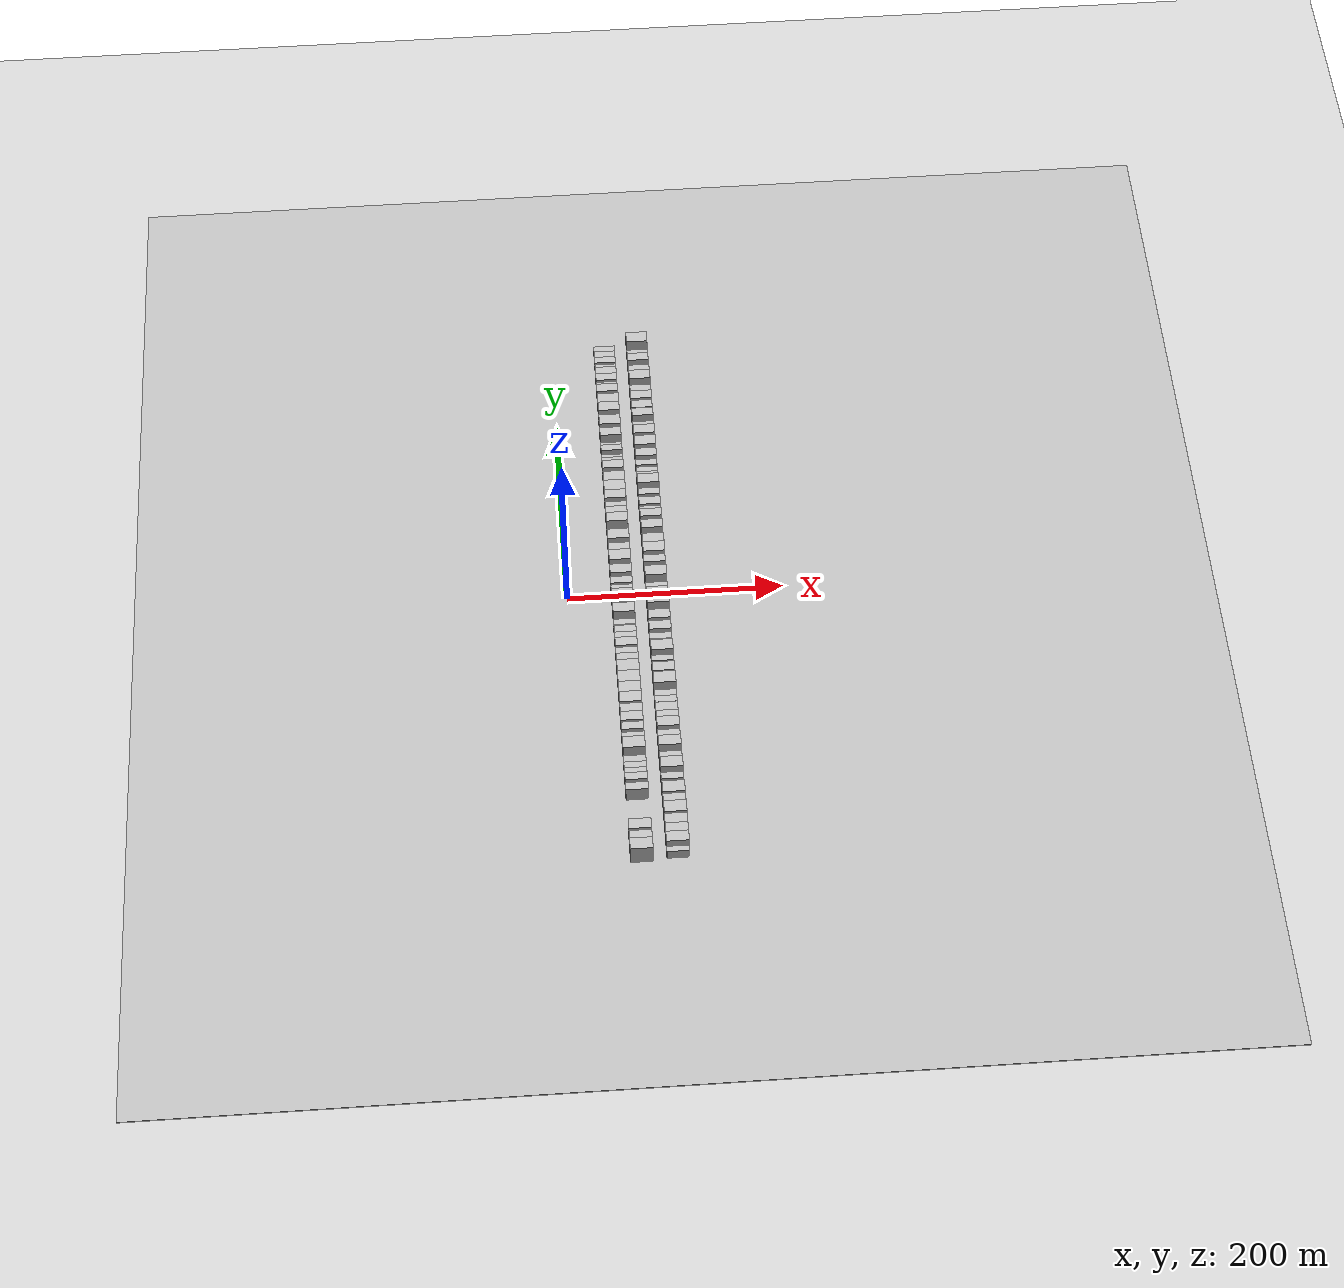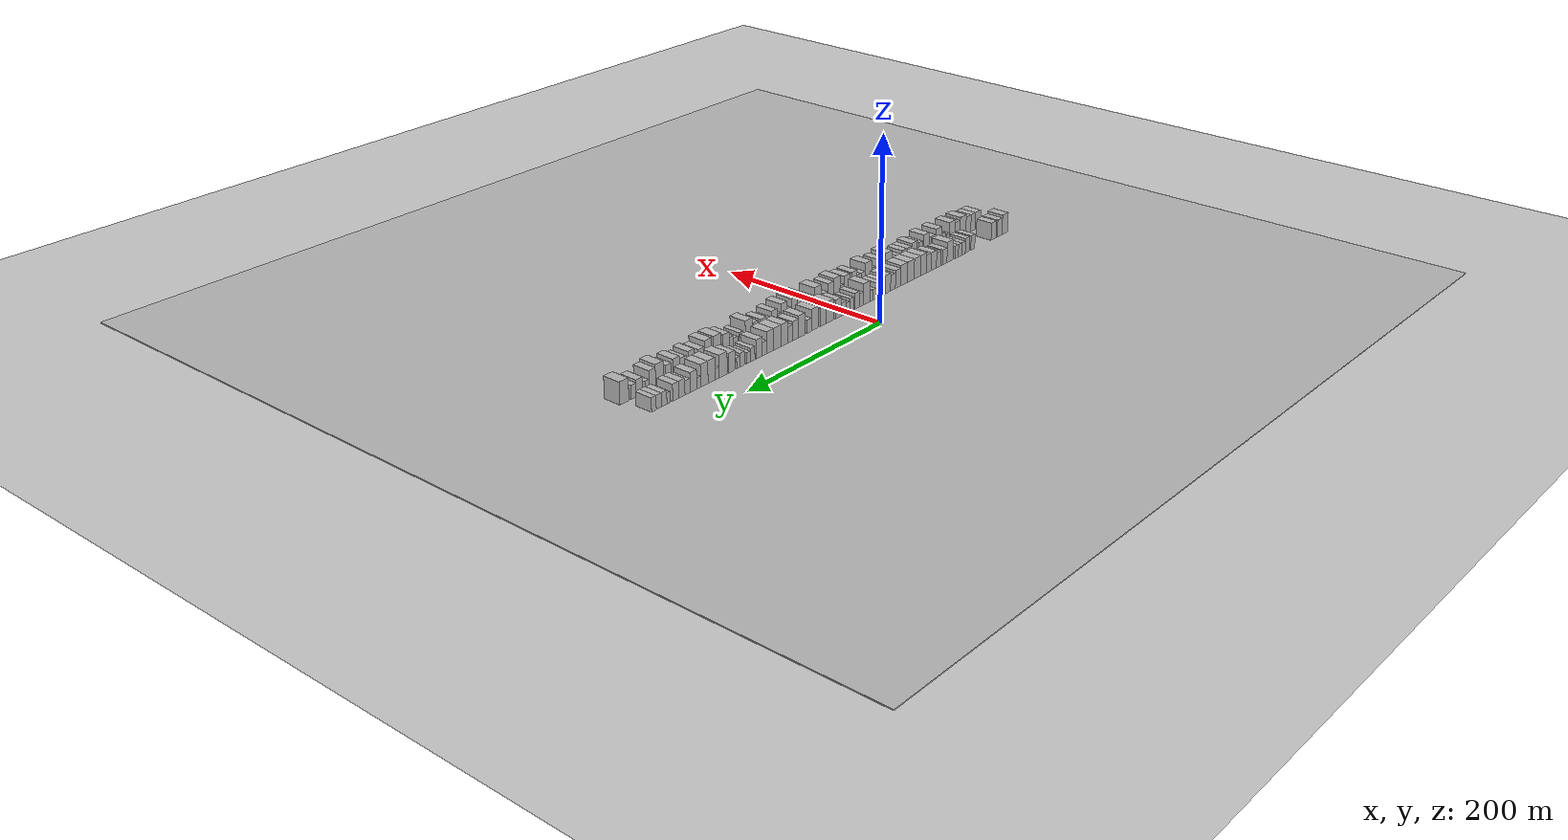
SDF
<?xml version="1.0" encoding="utf-8"?>

<sdf version="1.6">

   <world name="default">

      <gui fullscreen="0">

         <camera name="user_camera">

            <pose>-15 0 4.57585 0 0 0</pose>

            <view_controller>orbit</view_controller>

         </camera>

      </gui>

      <scene>

         <sky>

           <clouds>

             <speed>12</speed>

           </clouds>

         </sky>

         <ambient>0.4 0.4 0.4 1</ambient>

         <background>0.7 0.7 0.7 1</background>

         <shadows>1</shadows>

      </scene>

      <gravity>0 0 -9.8066</gravity>

      <magnetic_field>6e-06 2.3e-05 -4.2e-05</magnetic_field>

      <physics default="0" name="default_physics" type="ode">

         <ode>

            <solver>

               <type>quick</type>

               <iters>10</iters>

               <sor>1.0</sor>

               <use_dynamic_moi_rescaling>0</use_dynamic_moi_rescaling>

            </solver>

            <constraints>

               <cfm>0</cfm>

               <erp>0.2</erp>

               <contact_max_correcting_vel>100</contact_max_correcting_vel>

               <contact_surface_layer>0.001</contact_surface_layer>

            </constraints>

         </ode>

         <max_step_size>0.004</max_step_size>

         <real_time_factor>1</real_time_factor>

         <real_time_update_rate>250</real_time_update_rate>

      </physics>

      <light name="sun" type="directional">

         <cast_shadows>1</cast_shadows>

         <pose>0 0 10 0 0 0</pose>

         <diffuse>0.8 0.8 0.8 1</diffuse>

         <specular>0.2 0.2 0.2 1</specular>

         <attenuation>

            <range>1000</range>

            <constant>0.9</constant>

            <linear>0.01</linear>

            <quadratic>0.001</quadratic>

         </attenuation>

         <direction>-0.5 0.1 -0.9</direction>

      </light>

      <include>

         <name>ground_plane_1</name>

         <uri>model://HANNAS_ground_plane</uri>

         <pose>0 0 0  0 0 0</pose>

      </include>

      <include>

         <name>ground_plane_2</name>

         <uri>model://HANNAS_ground_plane</uri>

         <pose>100 0 0  0 0 0</pose>

      </include>

      <model name="building_1">

         <static>1</static>

         <pose frame="">50.0000 -278.4930 0 0.000000 0.000000 0.000000</pose>

         <link name="link">

            <pose frame="">0 0 12.00 0 0 0</pose>

            <collision name="collision">

               <geometry>

                  <box>

                     <size>20.0000 11.0139 24.0000</size>

                  </box>

               </geometry>

               <max_contacts>10</max_contacts>

               <surface>

                  <contact>

                     <ode/>

                  </contact>

                  <bounce/>

                  <friction>

                     <torsional>

                        <ode/>

                     </torsional>

                     <ode/>

                  </friction>

               </surface>

            </collision>

            <visual name="visual">

               <cast_shadows>0</cast_shadows>

               <geometry>

                  <box>

                     <size>20.0000 11.0139 24.0000</size>

                  </box>

               </geometry>

               <material>

                  <script>

                     <uri>model://HANNAS_wall/materials/scripts</uri>

                     <uri>model://HANNAS_wall/materials/textures</uri>

                     <name>vrc/HANNAS_wall</name>

                  </script>

               </material>

            </visual>

            <self_collide>0</self_collide>

            <enable_wind>0</enable_wind>

            <kinematic>0</kinematic>

         </link>

      </model>

      <model name="building_2">

         <static>1</static>

         <pose frame="">50.0000 -268.3517 0 0.000000 0.000000 0.000000</pose>

         <link name="link">

            <pose frame="">0 0 10.50 0 0 0</pose>

            <collision name="collision">

               <geometry>

                  <box>

                     <size>20.0000 9.2688 21.0000</size>

                  </box>

               </geometry>

               <max_contacts>10</max_contacts>

               <surface>

                  <contact>

                     <ode/>

                  </contact>

                  <bounce/>

                  <friction>

                     <torsional>

                        <ode/>

                     </torsional>

                     <ode/>

                  </friction>

               </surface>

            </collision>

            <visual name="visual">

               <cast_shadows>0</cast_shadows>

               <geometry>

                  <box>

                     <size>20.0000 9.2688 21.0000</size>

                  </box>

               </geometry>

               <material>

                  <script>

                     <uri>model://HANNAS_wall/materials/scripts</uri>

                     <uri>model://HANNAS_wall/materials/textures</uri>

                     <name>vrc/HANNAS_wall</name>

                  </script>

               </material>

            </visual>

            <self_collide>0</self_collide>

            <enable_wind>0</enable_wind>

            <kinematic>0</kinematic>

         </link>

      </model>

      <model name="building_3">

         <static>1</static>

         <pose frame="">50.0000 -256.8036 0 0.000000 0.000000 0.000000</pose>

         <link name="link">

            <pose frame="">0 0 10.50 0 0 0</pose>

            <collision name="collision">

               <geometry>

                  <box>

                     <size>20.0000 9.8273 21.0000</size>

                  </box>

               </geometry>

               <max_contacts>10</max_contacts>

               <surface>

                  <contact>

                     <ode/>

                  </contact>

                  <bounce/>

                  <friction>

                     <torsional>

                        <ode/>

                     </torsional>

                     <ode/>

                  </friction>

               </surface>

            </collision>

            <visual name="visual">

               <cast_shadows>0</cast_shadows>

               <geometry>

                  <box>

                     <size>20.0000 9.8273 21.0000</size>

                  </box>

               </geometry>

               <material>

                  <script>

                     <uri>model://HANNAS_wall/materials/scripts</uri>

                     <uri>model://HANNAS_wall/materials/textures</uri>

                     <name>vrc/HANNAS_wall</name>

                  </script>

               </material>

            </visual>

            <self_collide>0</self_collide>

            <enable_wind>0</enable_wind>

            <kinematic>0</kinematic>

         </link>

      </model>

      <model name="building_4">

         <static>1</static>

         <pose frame="">50.0000 -216.7169 0 0.000000 0.000000 0.000000</pose>

         <link name="link">

            <pose frame="">0 0 9.00 0 0 0</pose>

            <collision name="collision">

               <geometry>

                  <box>

                     <size>20.0000 7.4487 18.0000</size>

                  </box>

               </geometry>

               <max_contacts>10</max_contacts>

               <surface>

                  <contact>

                     <ode/>

                  </contact>

                  <bounce/>

                  <friction>

                     <torsional>

                        <ode/>

                     </torsional>

                     <ode/>

                  </friction>

               </surface>

            </collision>

            <visual name="visual">

               <cast_shadows>0</cast_shadows>

               <geometry>

                  <box>

                     <size>20.0000 7.4487 18.0000</size>

                  </box>

               </geometry>

               <material>

                  <script>

                     <uri>model://HANNAS_wall/materials/scripts</uri>

                     <uri>model://HANNAS_wall/materials/textures</uri>

                     <name>vrc/HANNAS_wall</name>

                  </script>

               </material>

            </visual>

            <self_collide>0</self_collide>

            <enable_wind>0</enable_wind>

            <kinematic>0</kinematic>

         </link>

      </model>

      <model name="building_5">

         <static>1</static>

         <pose frame="">50.0000 -206.3585 0 0.000000 0.000000 0.000000</pose>

         <link name="link">

            <pose frame="">0 0 9.00 0 0 0</pose>

            <collision name="collision">

               <geometry>

                  <box>

                     <size>20.0000 7.2680 18.0000</size>

                  </box>

               </geometry>

               <max_contacts>10</max_contacts>

               <surface>

                  <contact>

                     <ode/>

                  </contact>

                  <bounce/>

                  <friction>

                     <torsional>

                        <ode/>

                     </torsional>

                     <ode/>

                  </friction>

               </surface>

            </collision>

            <visual name="visual">

               <cast_shadows>0</cast_shadows>

               <geometry>

                  <box>

                     <size>20.0000 7.2680 18.0000</size>

                  </box>

               </geometry>

               <material>

                  <script>

                     <uri>model://HANNAS_wall/materials/scripts</uri>

                     <uri>model://HANNAS_wall/materials/textures</uri>

                     <name>vrc/HANNAS_wall</name>

                  </script>

               </material>

            </visual>

            <self_collide>0</self_collide>

            <enable_wind>0</enable_wind>

            <kinematic>0</kinematic>

         </link>

      </model>

      <model name="building_6">

         <static>1</static>

         <pose frame="">50.0000 -199.2980 0 0.000000 0.000000 0.000000</pose>

         <link name="link">

            <pose frame="">0 0 7.50 0 0 0</pose>

            <collision name="collision">

               <geometry>

                  <box>

                     <size>20.0000 6.8530 15.0000</size>

                  </box>

               </geometry>

               <max_contacts>10</max_contacts>

               <surface>

                  <contact>

                     <ode/>

                  </contact>

                  <bounce/>

                  <friction>

                     <torsional>

                        <ode/>

                     </torsional>

                     <ode/>

                  </friction>

               </surface>

            </collision>

            <visual name="visual">

               <cast_shadows>0</cast_shadows>

               <geometry>

                  <box>

                     <size>20.0000 6.8530 15.0000</size>

                  </box>

               </geometry>

               <material>

                  <script>

                     <uri>model://HANNAS_wall/materials/scripts</uri>

                     <uri>model://HANNAS_wall/materials/textures</uri>

                     <name>vrc/HANNAS_wall</name>

                  </script>

               </material>

            </visual>

            <self_collide>0</self_collide>

            <enable_wind>0</enable_wind>

            <kinematic>0</kinematic>

         </link>

      </model>

      <model name="building_7">

         <static>1</static>

         <pose frame="">50.0000 -192.8294 0 0.000000 0.000000 0.000000</pose>

         <link name="link">

            <pose frame="">0 0 7.50 0 0 0</pose>

            <collision name="collision">

               <geometry>

                  <box>

                     <size>20.0000 6.0842 15.0000</size>

                  </box>

               </geometry>

               <max_contacts>10</max_contacts>

               <surface>

                  <contact>

                     <ode/>

                  </contact>

                  <bounce/>

                  <friction>

                     <torsional>

                        <ode/>

                     </torsional>

                     <ode/>

                  </friction>

               </surface>

            </collision>

            <visual name="visual">

               <cast_shadows>0</cast_shadows>

               <geometry>

                  <box>

                     <size>20.0000 6.0842 15.0000</size>

                  </box>

               </geometry>

               <material>

                  <script>

                     <uri>model://HANNAS_wall/materials/scripts</uri>

                     <uri>model://HANNAS_wall/materials/textures</uri>

                     <name>vrc/HANNAS_wall</name>

                  </script>

               </material>

            </visual>

            <self_collide>0</self_collide>

            <enable_wind>0</enable_wind>

            <kinematic>0</kinematic>

         </link>

      </model>

      <model name="building_8">

         <static>1</static>

         <pose frame="">50.0000 -186.5375 0 0.000000 0.000000 0.000000</pose>

         <link name="link">

            <pose frame="">0 0 7.50 0 0 0</pose>

            <collision name="collision">

               <geometry>

                  <box>

                     <size>20.0000 6.4996 15.0000</size>

                  </box>

               </geometry>

               <max_contacts>10</max_contacts>

               <surface>

                  <contact>

                     <ode/>

                  </contact>

                  <bounce/>

                  <friction>

                     <torsional>

                        <ode/>

                     </torsional>

                     <ode/>

                  </friction>

               </surface>

            </collision>

            <visual name="visual">

               <cast_shadows>0</cast_shadows>

               <geometry>

                  <box>

                     <size>20.0000 6.4996 15.0000</size>

                  </box>

               </geometry>

               <material>

                  <script>

                     <uri>model://HANNAS_wall/materials/scripts</uri>

                     <uri>model://HANNAS_wall/materials/textures</uri>

                     <name>vrc/HANNAS_wall</name>

                  </script>

               </material>

            </visual>

            <self_collide>0</self_collide>

            <enable_wind>0</enable_wind>

            <kinematic>0</kinematic>

         </link>

      </model>

      <model name="building_9">

         <static>1</static>

         <pose frame="">50.0000 -174.5439 0 0.000000 0.000000 0.000000</pose>

         <link name="link">

            <pose frame="">0 0 12.00 0 0 0</pose>

            <collision name="collision">

               <geometry>

                  <box>

                     <size>20.0000 11.4876 24.0000</size>

                  </box>

               </geometry>

               <max_contacts>10</max_contacts>

               <surface>

                  <contact>

                     <ode/>

                  </contact>

                  <bounce/>

                  <friction>

                     <torsional>

                        <ode/>

                     </torsional>

                     <ode/>

                  </friction>

               </surface>

            </collision>

            <visual name="visual">

               <cast_shadows>0</cast_shadows>

               <geometry>

                  <box>

                     <size>20.0000 11.4876 24.0000</size>

                  </box>

               </geometry>

               <material>

                  <script>

                     <uri>model://HANNAS_wall/materials/scripts</uri>

                     <uri>model://HANNAS_wall/materials/textures</uri>

                     <name>vrc/HANNAS_wall</name>

                  </script>

               </material>

            </visual>

            <self_collide>0</self_collide>

            <enable_wind>0</enable_wind>

            <kinematic>0</kinematic>

         </link>

      </model>

      <model name="building_10">

         <static>1</static>

         <pose frame="">50.0000 -164.6084 0 0.000000 0.000000 0.000000</pose>

         <link name="link">

            <pose frame="">0 0 9.00 0 0 0</pose>

            <collision name="collision">

               <geometry>

                  <box>

                     <size>20.0000 8.3834 18.0000</size>

                  </box>

               </geometry>

               <max_contacts>10</max_contacts>

               <surface>

                  <contact>

                     <ode/>

                  </contact>

                  <bounce/>

                  <friction>

                     <torsional>

                        <ode/>

                     </torsional>

                     <ode/>

                  </friction>

               </surface>

            </collision>

            <visual name="visual">

               <cast_shadows>0</cast_shadows>

               <geometry>

                  <box>

                     <size>20.0000 8.3834 18.0000</size>

                  </box>

               </geometry>

               <material>

                  <script>

                     <uri>model://HANNAS_wall/materials/scripts</uri>

                     <uri>model://HANNAS_wall/materials/textures</uri>

                     <name>vrc/HANNAS_wall</name>

                  </script>

               </material>

            </visual>

            <self_collide>0</self_collide>

            <enable_wind>0</enable_wind>

            <kinematic>0</kinematic>

         </link>

      </model>

      <model name="building_11">

         <static>1</static>

         <pose frame="">50.0000 -153.5251 0 0.000000 0.000000 0.000000</pose>

         <link name="link">

            <pose frame="">0 0 9.00 0 0 0</pose>

            <collision name="collision">

               <geometry>

                  <box>

                     <size>20.0000 7.7832 18.0000</size>

                  </box>

               </geometry>

               <max_contacts>10</max_contacts>

               <surface>

                  <contact>

                     <ode/>

                  </contact>

                  <bounce/>

                  <friction>

                     <torsional>

                        <ode/>

                     </torsional>

                     <ode/>

                  </friction>

               </surface>

            </collision>

            <visual name="visual">

               <cast_shadows>0</cast_shadows>

               <geometry>

                  <box>

                     <size>20.0000 7.7832 18.0000</size>

                  </box>

               </geometry>

               <material>

                  <script>

                     <uri>model://HANNAS_wall/materials/scripts</uri>

                     <uri>model://HANNAS_wall/materials/textures</uri>

                     <name>vrc/HANNAS_wall</name>

                  </script>

               </material>

            </visual>

            <self_collide>0</self_collide>

            <enable_wind>0</enable_wind>

            <kinematic>0</kinematic>

         </link>

      </model>

      <model name="building_12">

         <static>1</static>

         <pose frame="">50.0000 -144.9641 0 0.000000 0.000000 0.000000</pose>

         <link name="link">

            <pose frame="">0 0 10.50 0 0 0</pose>

            <collision name="collision">

               <geometry>

                  <box>

                     <size>20.0000 9.3388 21.0000</size>

                  </box>

               </geometry>

               <max_contacts>10</max_contacts>

               <surface>

                  <contact>

                     <ode/>

                  </contact>

                  <bounce/>

                  <friction>

                     <torsional>

                        <ode/>

                     </torsional>

                     <ode/>

                  </friction>

               </surface>

            </collision>

            <visual name="visual">

               <cast_shadows>0</cast_shadows>

               <geometry>

                  <box>

                     <size>20.0000 9.3388 21.0000</size>

                  </box>

               </geometry>

               <material>

                  <script>

                     <uri>model://HANNAS_wall/materials/scripts</uri>

                     <uri>model://HANNAS_wall/materials/textures</uri>

                     <name>vrc/HANNAS_wall</name>

                  </script>

               </material>

            </visual>

            <self_collide>0</self_collide>

            <enable_wind>0</enable_wind>

            <kinematic>0</kinematic>

         </link>

      </model>

      <model name="building_13">

         <static>1</static>

         <pose frame="">50.0000 -136.0853 0 0.000000 0.000000 0.000000</pose>

         <link name="link">

            <pose frame="">0 0 10.50 0 0 0</pose>

            <collision name="collision">

               <geometry>

                  <box>

                     <size>20.0000 8.4189 21.0000</size>

                  </box>

               </geometry>

               <max_contacts>10</max_contacts>

               <surface>

                  <contact>

                     <ode/>

                  </contact>

                  <bounce/>

                  <friction>

                     <torsional>

                        <ode/>

                     </torsional>

                     <ode/>

                  </friction>

               </surface>

            </collision>

            <visual name="visual">

               <cast_shadows>0</cast_shadows>

               <geometry>

                  <box>

                     <size>20.0000 8.4189 21.0000</size>

                  </box>

               </geometry>

               <material>

                  <script>

                     <uri>model://HANNAS_wall/materials/scripts</uri>

                     <uri>model://HANNAS_wall/materials/textures</uri>

                     <name>vrc/HANNAS_wall</name>

                  </script>

               </material>

            </visual>

            <self_collide>0</self_collide>

            <enable_wind>0</enable_wind>

            <kinematic>0</kinematic>

         </link>

      </model>

      <model name="building_14">

         <static>1</static>

         <pose frame="">50.0000 -126.4248 0 0.000000 0.000000 0.000000</pose>

         <link name="link">

            <pose frame="">0 0 12.00 0 0 0</pose>

            <collision name="collision">

               <geometry>

                  <box>

                     <size>20.0000 10.9022 24.0000</size>

                  </box>

               </geometry>

               <max_contacts>10</max_contacts>

               <surface>

                  <contact>

                     <ode/>

                  </contact>

                  <bounce/>

                  <friction>

                     <torsional>

                        <ode/>

                     </torsional>

                     <ode/>

                  </friction>

               </surface>

            </collision>

            <visual name="visual">

               <cast_shadows>0</cast_shadows>

               <geometry>

                  <box>

                     <size>20.0000 10.9022 24.0000</size>

                  </box>

               </geometry>

               <material>

                  <script>

                     <uri>model://HANNAS_wall/materials/scripts</uri>

                     <uri>model://HANNAS_wall/materials/textures</uri>

                     <name>vrc/HANNAS_wall</name>

                  </script>

               </material>

            </visual>

            <self_collide>0</self_collide>

            <enable_wind>0</enable_wind>

            <kinematic>0</kinematic>

         </link>

      </model>

      <model name="building_15">

         <static>1</static>

         <pose frame="">50.0000 -115.5003 0 0.000000 0.000000 0.000000</pose>

         <link name="link">

            <pose frame="">0 0 12.00 0 0 0</pose>

            <collision name="collision">

               <geometry>

                  <box>

                     <size>20.0000 10.9469 24.0000</size>

                  </box>

               </geometry>

               <max_contacts>10</max_contacts>

               <surface>

                  <contact>

                     <ode/>

                  </contact>

                  <bounce/>

                  <friction>

                     <torsional>

                        <ode/>

                     </torsional>

                     <ode/>

                  </friction>

               </surface>

            </collision>

            <visual name="visual">

               <cast_shadows>0</cast_shadows>

               <geometry>

                  <box>

                     <size>20.0000 10.9469 24.0000</size>

                  </box>

               </geometry>

               <material>

                  <script>

                     <uri>model://HANNAS_wall/materials/scripts</uri>

                     <uri>model://HANNAS_wall/materials/textures</uri>

                     <name>vrc/HANNAS_wall</name>

                  </script>

               </material>

            </visual>

            <self_collide>0</self_collide>

            <enable_wind>0</enable_wind>

            <kinematic>0</kinematic>

         </link>

      </model>

      <model name="building_16">

         <static>1</static>

         <pose frame="">50.0000 -104.1812 0 0.000000 0.000000 0.000000</pose>

         <link name="link">

            <pose frame="">0 0 12.00 0 0 0</pose>

            <collision name="collision">

               <geometry>

                  <box>

                     <size>20.0000 11.6913 24.0000</size>

                  </box>

               </geometry>

               <max_contacts>10</max_contacts>

               <surface>

                  <contact>

                     <ode/>

                  </contact>

                  <bounce/>

                  <friction>

                     <torsional>

                        <ode/>

                     </torsional>

                     <ode/>

                  </friction>

               </surface>

            </collision>

            <visual name="visual">

               <cast_shadows>0</cast_shadows>

               <geometry>

                  <box>

                     <size>20.0000 11.6913 24.0000</size>

                  </box>

               </geometry>

               <material>

                  <script>

                     <uri>model://HANNAS_wall/materials/scripts</uri>

                     <uri>model://HANNAS_wall/materials/textures</uri>

                     <name>vrc/HANNAS_wall</name>

                  </script>

               </material>

            </visual>

            <self_collide>0</self_collide>

            <enable_wind>0</enable_wind>

            <kinematic>0</kinematic>

         </link>

      </model>

      <model name="building_17">

         <static>1</static>

         <pose frame="">50.0000 -92.3757 0 0.000000 0.000000 0.000000</pose>

         <link name="link">

            <pose frame="">0 0 12.00 0 0 0</pose>

            <collision name="collision">

               <geometry>

                  <box>

                     <size>20.0000 11.9197 24.0000</size>

                  </box>

               </geometry>

               <max_contacts>10</max_contacts>

               <surface>

                  <contact>

                     <ode/>

                  </contact>

                  <bounce/>

                  <friction>

                     <torsional>

                        <ode/>

                     </torsional>

                     <ode/>

                  </friction>

               </surface>

            </collision>

            <visual name="visual">

               <cast_shadows>0</cast_shadows>

               <geometry>

                  <box>

                     <size>20.0000 11.9197 24.0000</size>

                  </box>

               </geometry>

               <material>

                  <script>

                     <uri>model://HANNAS_wall/materials/scripts</uri>

                     <uri>model://HANNAS_wall/materials/textures</uri>

                     <name>vrc/HANNAS_wall</name>

                  </script>

               </material>

            </visual>

            <self_collide>0</self_collide>

            <enable_wind>0</enable_wind>

            <kinematic>0</kinematic>

         </link>

      </model>

      <model name="building_18">

         <static>1</static>

         <pose frame="">50.0000 -81.9634 0 0.000000 0.000000 0.000000</pose>

         <link name="link">

            <pose frame="">0 0 10.50 0 0 0</pose>

            <collision name="collision">

               <geometry>

                  <box>

                     <size>20.0000 8.9050 21.0000</size>

                  </box>

               </geometry>

               <max_contacts>10</max_contacts>

               <surface>

                  <contact>

                     <ode/>

                  </contact>

                  <bounce/>

                  <friction>

                     <torsional>

                        <ode/>

                     </torsional>

                     <ode/>

                  </friction>

               </surface>

            </collision>

            <visual name="visual">

               <cast_shadows>0</cast_shadows>

               <geometry>

                  <box>

                     <size>20.0000 8.9050 21.0000</size>

                  </box>

               </geometry>

               <material>

                  <script>

                     <uri>model://HANNAS_wall/materials/scripts</uri>

                     <uri>model://HANNAS_wall/materials/textures</uri>

                     <name>vrc/HANNAS_wall</name>

                  </script>

               </material>

            </visual>

            <self_collide>0</self_collide>

            <enable_wind>0</enable_wind>

            <kinematic>0</kinematic>

         </link>

      </model>

      <model name="building_19">

         <static>1</static>

         <pose frame="">50.0000 -73.3345 0 0.000000 0.000000 0.000000</pose>

         <link name="link">

            <pose frame="">0 0 9.00 0 0 0</pose>

            <collision name="collision">

               <geometry>

                  <box>

                     <size>20.0000 8.3528 18.0000</size>

                  </box>

               </geometry>

               <max_contacts>10</max_contacts>

               <surface>

                  <contact>

                     <ode/>

                  </contact>

                  <bounce/>

                  <friction>

                     <torsional>

                        <ode/>

                     </torsional>

                     <ode/>

                  </friction>

               </surface>

            </collision>

            <visual name="visual">

               <cast_shadows>0</cast_shadows>

               <geometry>

                  <box>

                     <size>20.0000 8.3528 18.0000</size>

                  </box>

               </geometry>

               <material>

                  <script>

                     <uri>model://HANNAS_wall/materials/scripts</uri>

                     <uri>model://HANNAS_wall/materials/textures</uri>

                     <name>vrc/HANNAS_wall</name>

                  </script>

               </material>

            </visual>

            <self_collide>0</self_collide>

            <enable_wind>0</enable_wind>

            <kinematic>0</kinematic>

         </link>

      </model>

      <model name="building_20">

         <static>1</static>

         <pose frame="">50.0000 -64.6351 0 0.000000 0.000000 0.000000</pose>

         <link name="link">

            <pose frame="">0 0 10.50 0 0 0</pose>

            <collision name="collision">

               <geometry>

                  <box>

                     <size>20.0000 9.0460 21.0000</size>

                  </box>

               </geometry>

               <max_contacts>10</max_contacts>

               <surface>

                  <contact>

                     <ode/>

                  </contact>

                  <bounce/>

                  <friction>

                     <torsional>

                        <ode/>

                     </torsional>

                     <ode/>

                  </friction>

               </surface>

            </collision>

            <visual name="visual">

               <cast_shadows>0</cast_shadows>

               <geometry>

                  <box>

                     <size>20.0000 9.0460 21.0000</size>

                  </box>

               </geometry>

               <material>

                  <script>

                     <uri>model://HANNAS_wall/materials/scripts</uri>

                     <uri>model://HANNAS_wall/materials/textures</uri>

                     <name>vrc/HANNAS_wall</name>

                  </script>

               </material>

            </visual>

            <self_collide>0</self_collide>

            <enable_wind>0</enable_wind>

            <kinematic>0</kinematic>

         </link>

      </model>

      <model name="building_21">

         <static>1</static>

         <pose frame="">50.0000 -56.1918 0 0.000000 0.000000 0.000000</pose>

         <link name="link">

            <pose frame="">0 0 9.00 0 0 0</pose>

            <collision name="collision">

               <geometry>

                  <box>

                     <size>20.0000 7.8406 18.0000</size>

                  </box>

               </geometry>

               <max_contacts>10</max_contacts>

               <surface>

                  <contact>

                     <ode/>

                  </contact>

                  <bounce/>

                  <friction>

                     <torsional>

                        <ode/>

                     </torsional>

                     <ode/>

                  </friction>

               </surface>

            </collision>

            <visual name="visual">

               <cast_shadows>0</cast_shadows>

               <geometry>

                  <box>

                     <size>20.0000 7.8406 18.0000</size>

                  </box>

               </geometry>

               <material>

                  <script>

                     <uri>model://HANNAS_wall/materials/scripts</uri>

                     <uri>model://HANNAS_wall/materials/textures</uri>

                     <name>vrc/HANNAS_wall</name>

                  </script>

               </material>

            </visual>

            <self_collide>0</self_collide>

            <enable_wind>0</enable_wind>

            <kinematic>0</kinematic>

         </link>

      </model>

      <model name="building_22">

         <static>1</static>

         <pose frame="">50.0000 -48.6585 0 0.000000 0.000000 0.000000</pose>

         <link name="link">

            <pose frame="">0 0 9.00 0 0 0</pose>

            <collision name="collision">

               <geometry>

                  <box>

                     <size>20.0000 7.2261 18.0000</size>

                  </box>

               </geometry>

               <max_contacts>10</max_contacts>

               <surface>

                  <contact>

                     <ode/>

                  </contact>

                  <bounce/>

                  <friction>

                     <torsional>

                        <ode/>

                     </torsional>

                     <ode/>

                  </friction>

               </surface>

            </collision>

            <visual name="visual">

               <cast_shadows>0</cast_shadows>

               <geometry>

                  <box>

                     <size>20.0000 7.2261 18.0000</size>

                  </box>

               </geometry>

               <material>

                  <script>

                     <uri>model://HANNAS_wall/materials/scripts</uri>

                     <uri>model://HANNAS_wall/materials/textures</uri>

                     <name>vrc/HANNAS_wall</name>

                  </script>

               </material>

            </visual>

            <self_collide>0</self_collide>

            <enable_wind>0</enable_wind>

            <kinematic>0</kinematic>

         </link>

      </model>

      <model name="building_23">

         <static>1</static>

         <pose frame="">50.0000 -42.4910 0 0.000000 0.000000 0.000000</pose>

         <link name="link">

            <pose frame="">0 0 6.00 0 0 0</pose>

            <collision name="collision">

               <geometry>

                  <box>

                     <size>20.0000 5.1089 12.0000</size>

                  </box>

               </geometry>

               <max_contacts>10</max_contacts>

               <surface>

                  <contact>

                     <ode/>

                  </contact>

                  <bounce/>

                  <friction>

                     <torsional>

                        <ode/>

                     </torsional>

                     <ode/>

                  </friction>

               </surface>

            </collision>

            <visual name="visual">

               <cast_shadows>0</cast_shadows>

               <geometry>

                  <box>

                     <size>20.0000 5.1089 12.0000</size>

                  </box>

               </geometry>

               <material>

                  <script>

                     <uri>model://HANNAS_wall/materials/scripts</uri>

                     <uri>model://HANNAS_wall/materials/textures</uri>

                     <name>vrc/HANNAS_wall</name>

                  </script>

               </material>

            </visual>

            <self_collide>0</self_collide>

            <enable_wind>0</enable_wind>

            <kinematic>0</kinematic>

         </link>

      </model>

      <model name="building_24">

         <static>1</static>

         <pose frame="">50.0000 -36.9791 0 0.000000 0.000000 0.000000</pose>

         <link name="link">

            <pose frame="">0 0 6.00 0 0 0</pose>

            <collision name="collision">

               <geometry>

                  <box>

                     <size>20.0000 5.9149 12.0000</size>

                  </box>

               </geometry>

               <max_contacts>10</max_contacts>

               <surface>

                  <contact>

                     <ode/>

                  </contact>

                  <bounce/>

                  <friction>

                     <torsional>

                        <ode/>

                     </torsional>

                     <ode/>

                  </friction>

               </surface>

            </collision>

            <visual name="visual">

               <cast_shadows>0</cast_shadows>

               <geometry>

                  <box>

                     <size>20.0000 5.9149 12.0000</size>

                  </box>

               </geometry>

               <material>

                  <script>

                     <uri>model://HANNAS_wall/materials/scripts</uri>

                     <uri>model://HANNAS_wall/materials/textures</uri>

                     <name>vrc/HANNAS_wall</name>

                  </script>

               </material>

            </visual>

            <self_collide>0</self_collide>

            <enable_wind>0</enable_wind>

            <kinematic>0</kinematic>

         </link>

      </model>

      <model name="building_25">

         <static>1</static>

         <pose frame="">50.0000 -28.9703 0 0.000000 0.000000 0.000000</pose>

         <link name="link">

            <pose frame="">0 0 12.00 0 0 0</pose>

            <collision name="collision">

               <geometry>

                  <box>

                     <size>20.0000 10.1026 24.0000</size>

                  </box>

               </geometry>

               <max_contacts>10</max_contacts>

               <surface>

                  <contact>

                     <ode/>

                  </contact>

                  <bounce/>

                  <friction>

                     <torsional>

                        <ode/>

                     </torsional>

                     <ode/>

                  </friction>

               </surface>

            </collision>

            <visual name="visual">

               <cast_shadows>0</cast_shadows>

               <geometry>

                  <box>

                     <size>20.0000 10.1026 24.0000</size>

                  </box>

               </geometry>

               <material>

                  <script>

                     <uri>model://HANNAS_wall/materials/scripts</uri>

                     <uri>model://HANNAS_wall/materials/textures</uri>

                     <name>vrc/HANNAS_wall</name>

                  </script>

               </material>

            </visual>

            <self_collide>0</self_collide>

            <enable_wind>0</enable_wind>

            <kinematic>0</kinematic>

         </link>

      </model>

      <model name="building_26">

         <static>1</static>

         <pose frame="">50.0000 -20.5697 0 0.000000 0.000000 0.000000</pose>

         <link name="link">

            <pose frame="">0 0 7.50 0 0 0</pose>

            <collision name="collision">

               <geometry>

                  <box>

                     <size>20.0000 6.6987 15.0000</size>

                  </box>

               </geometry>

               <max_contacts>10</max_contacts>

               <surface>

                  <contact>

                     <ode/>

                  </contact>

                  <bounce/>

                  <friction>

                     <torsional>

                        <ode/>

                     </torsional>

                     <ode/>

                  </friction>

               </surface>

            </collision>

            <visual name="visual">

               <cast_shadows>0</cast_shadows>

               <geometry>

                  <box>

                     <size>20.0000 6.6987 15.0000</size>

                  </box>

               </geometry>

               <material>

                  <script>

                     <uri>model://HANNAS_wall/materials/scripts</uri>

                     <uri>model://HANNAS_wall/materials/textures</uri>

                     <name>vrc/HANNAS_wall</name>

                  </script>

               </material>

            </visual>

            <self_collide>0</self_collide>

            <enable_wind>0</enable_wind>

            <kinematic>0</kinematic>

         </link>

      </model>

      <model name="building_27">

         <static>1</static>

         <pose frame="">50.0000 -13.3778 0 0.000000 0.000000 0.000000</pose>

         <link name="link">

            <pose frame="">0 0 9.00 0 0 0</pose>

            <collision name="collision">

               <geometry>

                  <box>

                     <size>20.0000 7.6851 18.0000</size>

                  </box>

               </geometry>

               <max_contacts>10</max_contacts>

               <surface>

                  <contact>

                     <ode/>

                  </contact>

                  <bounce/>

                  <friction>

                     <torsional>

                        <ode/>

                     </torsional>

                     <ode/>

                  </friction>

               </surface>

            </collision>

            <visual name="visual">

               <cast_shadows>0</cast_shadows>

               <geometry>

                  <box>

                     <size>20.0000 7.6851 18.0000</size>

                  </box>

               </geometry>

               <material>

                  <script>

                     <uri>model://HANNAS_wall/materials/scripts</uri>

                     <uri>model://HANNAS_wall/materials/textures</uri>

                     <name>vrc/HANNAS_wall</name>

                  </script>

               </material>

            </visual>

            <self_collide>0</self_collide>

            <enable_wind>0</enable_wind>

            <kinematic>0</kinematic>

         </link>

      </model>

      <model name="building_28">

         <static>1</static>

         <pose frame="">50.0000 -4.5084 0 0.000000 0.000000 0.000000</pose>

         <link name="link">

            <pose frame="">0 0 7.50 0 0 0</pose>

            <collision name="collision">

               <geometry>

                  <box>

                     <size>20.0000 6.0537 15.0000</size>

                  </box>

               </geometry>

               <max_contacts>10</max_contacts>

               <surface>

                  <contact>

                     <ode/>

                  </contact>

                  <bounce/>

                  <friction>

                     <torsional>

                        <ode/>

                     </torsional>

                     <ode/>

                  </friction>

               </surface>

            </collision>

            <visual name="visual">

               <cast_shadows>0</cast_shadows>

               <geometry>

                  <box>

                     <size>20.0000 6.0537 15.0000</size>

                  </box>

               </geometry>

               <material>

                  <script>

                     <uri>model://HANNAS_wall/materials/scripts</uri>

                     <uri>model://HANNAS_wall/materials/textures</uri>

                     <name>vrc/HANNAS_wall</name>

                  </script>

               </material>

            </visual>

            <self_collide>0</self_collide>

            <enable_wind>0</enable_wind>

            <kinematic>0</kinematic>

         </link>

      </model>

      <model name="building_29">

         <static>1</static>

         <pose frame="">50.0000 1.4817 0 0.000000 0.000000 0.000000</pose>

         <link name="link">

            <pose frame="">0 0 6.00 0 0 0</pose>

            <collision name="collision">

               <geometry>

                  <box>

                     <size>20.0000 5.9267 12.0000</size>

                  </box>

               </geometry>

               <max_contacts>10</max_contacts>

               <surface>

                  <contact>

                     <ode/>

                  </contact>

                  <bounce/>

                  <friction>

                     <torsional>

                        <ode/>

                     </torsional>

                     <ode/>

                  </friction>

               </surface>

            </collision>

            <visual name="visual">

               <cast_shadows>0</cast_shadows>

               <geometry>

                  <box>

                     <size>20.0000 5.9267 12.0000</size>

                  </box>

               </geometry>

               <material>

                  <script>

                     <uri>model://HANNAS_wall/materials/scripts</uri>

                     <uri>model://HANNAS_wall/materials/textures</uri>

                     <name>vrc/HANNAS_wall</name>

                  </script>

               </material>

            </visual>

            <self_collide>0</self_collide>

            <enable_wind>0</enable_wind>

            <kinematic>0</kinematic>

         </link>

      </model>

      <model name="building_30">

         <static>1</static>

         <pose frame="">50.0000 8.1328 0 0.000000 0.000000 0.000000</pose>

         <link name="link">

            <pose frame="">0 0 7.50 0 0 0</pose>

            <collision name="collision">

               <geometry>

                  <box>

                     <size>20.0000 7.3756 15.0000</size>

                  </box>

               </geometry>

               <max_contacts>10</max_contacts>

               <surface>

                  <contact>

                     <ode/>

                  </contact>

                  <bounce/>

                  <friction>

                     <torsional>

                        <ode/>

                     </torsional>

                     <ode/>

                  </friction>

               </surface>

            </collision>

            <visual name="visual">

               <cast_shadows>0</cast_shadows>

               <geometry>

                  <box>

                     <size>20.0000 7.3756 15.0000</size>

                  </box>

               </geometry>

               <material>

                  <script>

                     <uri>model://HANNAS_wall/materials/scripts</uri>

                     <uri>model://HANNAS_wall/materials/textures</uri>

                     <name>vrc/HANNAS_wall</name>

                  </script>

               </material>

            </visual>

            <self_collide>0</self_collide>

            <enable_wind>0</enable_wind>

            <kinematic>0</kinematic>

         </link>

      </model>

      <model name="building_31">

         <static>1</static>

         <pose frame="">50.0000 16.7723 0 0.000000 0.000000 0.000000</pose>

         <link name="link">

            <pose frame="">0 0 10.50 0 0 0</pose>

            <collision name="collision">

               <geometry>

                  <box>

                     <size>20.0000 9.9033 21.0000</size>

                  </box>

               </geometry>

               <max_contacts>10</max_contacts>

               <surface>

                  <contact>

                     <ode/>

                  </contact>

                  <bounce/>

                  <friction>

                     <torsional>

                        <ode/>

                     </torsional>

                     <ode/>

                  </friction>

               </surface>

            </collision>

            <visual name="visual">

               <cast_shadows>0</cast_shadows>

               <geometry>

                  <box>

                     <size>20.0000 9.9033 21.0000</size>

                  </box>

               </geometry>

               <material>

                  <script>

                     <uri>model://HANNAS_wall/materials/scripts</uri>

                     <uri>model://HANNAS_wall/materials/textures</uri>

                     <name>vrc/HANNAS_wall</name>

                  </script>

               </material>

            </visual>

            <self_collide>0</self_collide>

            <enable_wind>0</enable_wind>

            <kinematic>0</kinematic>

         </link>

      </model>

      <model name="building_32">

         <static>1</static>

         <pose frame="">50.0000 30.4309 0 0.000000 0.000000 0.000000</pose>

         <link name="link">

            <pose frame="">0 0 12.00 0 0 0</pose>

            <collision name="collision">

               <geometry>

                  <box>

                     <size>20.0000 11.4141 24.0000</size>

                  </box>

               </geometry>

               <max_contacts>10</max_contacts>

               <surface>

                  <contact>

                     <ode/>

                  </contact>

                  <bounce/>

                  <friction>

                     <torsional>

                        <ode/>

                     </torsional>

                     <ode/>

                  </friction>

               </surface>

            </collision>

            <visual name="visual">

               <cast_shadows>0</cast_shadows>

               <geometry>

                  <box>

                     <size>20.0000 11.4141 24.0000</size>

                  </box>

               </geometry>

               <material>

                  <script>

                     <uri>model://HANNAS_wall/materials/scripts</uri>

                     <uri>model://HANNAS_wall/materials/textures</uri>

                     <name>vrc/HANNAS_wall</name>

                  </script>

               </material>

            </visual>

            <self_collide>0</self_collide>

            <enable_wind>0</enable_wind>

            <kinematic>0</kinematic>

         </link>

      </model>

      <model name="building_33">

         <static>1</static>

         <pose frame="">50.0000 41.0678 0 0.000000 0.000000 0.000000</pose>

         <link name="link">

            <pose frame="">0 0 10.50 0 0 0</pose>

            <collision name="collision">

               <geometry>

                  <box>

                     <size>20.0000 9.8596 21.0000</size>

                  </box>

               </geometry>

               <max_contacts>10</max_contacts>

               <surface>

                  <contact>

                     <ode/>

                  </contact>

                  <bounce/>

                  <friction>

                     <torsional>

                        <ode/>

                     </torsional>

                     <ode/>

                  </friction>

               </surface>

            </collision>

            <visual name="visual">

               <cast_shadows>0</cast_shadows>

               <geometry>

                  <box>

                     <size>20.0000 9.8596 21.0000</size>

                  </box>

               </geometry>

               <material>

                  <script>

                     <uri>model://HANNAS_wall/materials/scripts</uri>

                     <uri>model://HANNAS_wall/materials/textures</uri>

                     <name>vrc/HANNAS_wall</name>

                  </script>

               </material>

            </visual>

            <self_collide>0</self_collide>

            <enable_wind>0</enable_wind>

            <kinematic>0</kinematic>

         </link>

      </model>

      <model name="building_34">

         <static>1</static>

         <pose frame="">50.0000 54.3550 0 0.000000 0.000000 0.000000</pose>

         <link name="link">

            <pose frame="">0 0 12.00 0 0 0</pose>

            <collision name="collision">

               <geometry>

                  <box>

                     <size>20.0000 10.7149 24.0000</size>

                  </box>

               </geometry>

               <max_contacts>10</max_contacts>

               <surface>

                  <contact>

                     <ode/>

                  </contact>

                  <bounce/>

                  <friction>

                     <torsional>

                        <ode/>

                     </torsional>

                     <ode/>

                  </friction>

               </surface>

            </collision>

            <visual name="visual">

               <cast_shadows>0</cast_shadows>

               <geometry>

                  <box>

                     <size>20.0000 10.7149 24.0000</size>

                  </box>

               </geometry>

               <material>

                  <script>

                     <uri>model://HANNAS_wall/materials/scripts</uri>

                     <uri>model://HANNAS_wall/materials/textures</uri>

                     <name>vrc/HANNAS_wall</name>

                  </script>

               </material>

            </visual>

            <self_collide>0</self_collide>

            <enable_wind>0</enable_wind>

            <kinematic>0</kinematic>

         </link>

      </model>

      <model name="building_35">

         <static>1</static>

         <pose frame="">50.0000 62.8601 0 0.000000 0.000000 0.000000</pose>

         <link name="link">

            <pose frame="">0 0 7.50 0 0 0</pose>

            <collision name="collision">

               <geometry>

                  <box>

                     <size>20.0000 6.2953 15.0000</size>

                  </box>

               </geometry>

               <max_contacts>10</max_contacts>

               <surface>

                  <contact>

                     <ode/>

                  </contact>

                  <bounce/>

                  <friction>

                     <torsional>

                        <ode/>

                     </torsional>

                     <ode/>

                  </friction>

               </surface>

            </collision>

            <visual name="visual">

               <cast_shadows>0</cast_shadows>

               <geometry>

                  <box>

                     <size>20.0000 6.2953 15.0000</size>

                  </box>

               </geometry>

               <material>

                  <script>

                     <uri>model://HANNAS_wall/materials/scripts</uri>

                     <uri>model://HANNAS_wall/materials/textures</uri>

                     <name>vrc/HANNAS_wall</name>

                  </script>

               </material>

            </visual>

            <self_collide>0</self_collide>

            <enable_wind>0</enable_wind>

            <kinematic>0</kinematic>

         </link>

      </model>

      <model name="building_36">

         <static>1</static>

         <pose frame="">50.0000 74.0234 0 0.000000 0.000000 0.000000</pose>

         <link name="link">

            <pose frame="">0 0 12.00 0 0 0</pose>

            <collision name="collision">

               <geometry>

                  <box>

                     <size>20.0000 10.0312 24.0000</size>

                  </box>

               </geometry>

               <max_contacts>10</max_contacts>

               <surface>

                  <contact>

                     <ode/>

                  </contact>

                  <bounce/>

                  <friction>

                     <torsional>

                        <ode/>

                     </torsional>

                     <ode/>

                  </friction>

               </surface>

            </collision>

            <visual name="visual">

               <cast_shadows>0</cast_shadows>

               <geometry>

                  <box>

                     <size>20.0000 10.0312 24.0000</size>

                  </box>

               </geometry>

               <material>

                  <script>

                     <uri>model://HANNAS_wall/materials/scripts</uri>

                     <uri>model://HANNAS_wall/materials/textures</uri>

                     <name>vrc/HANNAS_wall</name>

                  </script>

               </material>

            </visual>

            <self_collide>0</self_collide>

            <enable_wind>0</enable_wind>

            <kinematic>0</kinematic>

         </link>

      </model>

      <model name="building_37">

         <static>1</static>

         <pose frame="">50.0000 83.6397 0 0.000000 0.000000 0.000000</pose>

         <link name="link">

            <pose frame="">0 0 10.50 0 0 0</pose>

            <collision name="collision">

               <geometry>

                  <box>

                     <size>20.0000 9.2015 21.0000</size>

                  </box>

               </geometry>

               <max_contacts>10</max_contacts>

               <surface>

                  <contact>

                     <ode/>

                  </contact>

                  <bounce/>

                  <friction>

                     <torsional>

                        <ode/>

                     </torsional>

                     <ode/>

                  </friction>

               </surface>

            </collision>

            <visual name="visual">

               <cast_shadows>0</cast_shadows>

               <geometry>

                  <box>

                     <size>20.0000 9.2015 21.0000</size>

                  </box>

               </geometry>

               <material>

                  <script>

                     <uri>model://HANNAS_wall/materials/scripts</uri>

                     <uri>model://HANNAS_wall/materials/textures</uri>

                     <name>vrc/HANNAS_wall</name>

                  </script>

               </material>

            </visual>

            <self_collide>0</self_collide>

            <enable_wind>0</enable_wind>

            <kinematic>0</kinematic>

         </link>

      </model>

      <model name="building_38">

         <static>1</static>

         <pose frame="">50.0000 92.0039 0 0.000000 0.000000 0.000000</pose>

         <link name="link">

            <pose frame="">0 0 9.00 0 0 0</pose>

            <collision name="collision">

               <geometry>

                  <box>

                     <size>20.0000 7.5267 18.0000</size>

                  </box>

               </geometry>

               <max_contacts>10</max_contacts>

               <surface>

                  <contact>

                     <ode/>

                  </contact>

                  <bounce/>

                  <friction>

                     <torsional>

                        <ode/>

                     </torsional>

                     <ode/>

                  </friction>

               </surface>

            </collision>

            <visual name="visual">

               <cast_shadows>0</cast_shadows>

               <geometry>

                  <box>

                     <size>20.0000 7.5267 18.0000</size>

                  </box>

               </geometry>

               <material>

                  <script>

                     <uri>model://HANNAS_wall/materials/scripts</uri>

                     <uri>model://HANNAS_wall/materials/textures</uri>

                     <name>vrc/HANNAS_wall</name>

                  </script>

               </material>

            </visual>

            <self_collide>0</self_collide>

            <enable_wind>0</enable_wind>

            <kinematic>0</kinematic>

         </link>

      </model>

      <model name="building_39">

         <static>1</static>

         <pose frame="">50.0000 100.5890 0 0.000000 0.000000 0.000000</pose>

         <link name="link">

            <pose frame="">0 0 12.00 0 0 0</pose>

            <collision name="collision">

               <geometry>

                  <box>

                     <size>20.0000 9.6436 24.0000</size>

                  </box>

               </geometry>

               <max_contacts>10</max_contacts>

               <surface>

                  <contact>

                     <ode/>

                  </contact>

                  <bounce/>

                  <friction>

                     <torsional>

                        <ode/>

                     </torsional>

                     <ode/>

                  </friction>

               </surface>

            </collision>

            <visual name="visual">

               <cast_shadows>0</cast_shadows>

               <geometry>

                  <box>

                     <size>20.0000 9.6436 24.0000</size>

                  </box>

               </geometry>

               <material>

                  <script>

                     <uri>model://HANNAS_wall/materials/scripts</uri>

                     <uri>model://HANNAS_wall/materials/textures</uri>

                     <name>vrc/HANNAS_wall</name>

                  </script>

               </material>

            </visual>

            <self_collide>0</self_collide>

            <enable_wind>0</enable_wind>

            <kinematic>0</kinematic>

         </link>

      </model>

      <model name="building_40">

         <static>1</static>

         <pose frame="">50.0000 111.1085 0 0.000000 0.000000 0.000000</pose>

         <link name="link">

            <pose frame="">0 0 12.00 0 0 0</pose>

            <collision name="collision">

               <geometry>

                  <box>

                     <size>20.0000 11.3954 24.0000</size>

                  </box>

               </geometry>

               <max_contacts>10</max_contacts>

               <surface>

                  <contact>

                     <ode/>

                  </contact>

                  <bounce/>

                  <friction>

                     <torsional>

                        <ode/>

                     </torsional>

                     <ode/>

                  </friction>

               </surface>

            </collision>

            <visual name="visual">

               <cast_shadows>0</cast_shadows>

               <geometry>

                  <box>

                     <size>20.0000 11.3954 24.0000</size>

                  </box>

               </geometry>

               <material>

                  <script>

                     <uri>model://HANNAS_wall/materials/scripts</uri>

                     <uri>model://HANNAS_wall/materials/textures</uri>

                     <name>vrc/HANNAS_wall</name>

                  </script>

               </material>

            </visual>

            <self_collide>0</self_collide>

            <enable_wind>0</enable_wind>

            <kinematic>0</kinematic>

         </link>

      </model>

      <model name="building_41">

         <static>1</static>

         <pose frame="">50.0000 122.0105 0 0.000000 0.000000 0.000000</pose>

         <link name="link">

            <pose frame="">0 0 12.00 0 0 0</pose>

            <collision name="collision">

               <geometry>

                  <box>

                     <size>20.0000 10.4088 24.0000</size>

                  </box>

               </geometry>

               <max_contacts>10</max_contacts>

               <surface>

                  <contact>

                     <ode/>

                  </contact>

                  <bounce/>

                  <friction>

                     <torsional>

                        <ode/>

                     </torsional>

                     <ode/>

                  </friction>

               </surface>

            </collision>

            <visual name="visual">

               <cast_shadows>0</cast_shadows>

               <geometry>

                  <box>

                     <size>20.0000 10.4088 24.0000</size>

                  </box>

               </geometry>

               <material>

                  <script>

                     <uri>model://HANNAS_wall/materials/scripts</uri>

                     <uri>model://HANNAS_wall/materials/textures</uri>

                     <name>vrc/HANNAS_wall</name>

                  </script>

               </material>

            </visual>

            <self_collide>0</self_collide>

            <enable_wind>0</enable_wind>

            <kinematic>0</kinematic>

         </link>

      </model>

      <model name="building_42">

         <static>1</static>

         <pose frame="">50.0000 130.3506 0 0.000000 0.000000 0.000000</pose>

         <link name="link">

            <pose frame="">0 0 7.50 0 0 0</pose>

            <collision name="collision">

               <geometry>

                  <box>

                     <size>20.0000 6.2713 15.0000</size>

                  </box>

               </geometry>

               <max_contacts>10</max_contacts>

               <surface>

                  <contact>

                     <ode/>

                  </contact>

                  <bounce/>

                  <friction>

                     <torsional>

                        <ode/>

                     </torsional>

                     <ode/>

                  </friction>

               </surface>

            </collision>

            <visual name="visual">

               <cast_shadows>0</cast_shadows>

               <geometry>

                  <box>

                     <size>20.0000 6.2713 15.0000</size>

                  </box>

               </geometry>

               <material>

                  <script>

                     <uri>model://HANNAS_wall/materials/scripts</uri>

                     <uri>model://HANNAS_wall/materials/textures</uri>

                     <name>vrc/HANNAS_wall</name>

                  </script>

               </material>

            </visual>

            <self_collide>0</self_collide>

            <enable_wind>0</enable_wind>

            <kinematic>0</kinematic>

         </link>

      </model>

      <model name="building_43">

         <static>1</static>

         <pose frame="">50.0000 137.9851 0 0.000000 0.000000 0.000000</pose>

         <link name="link">

            <pose frame="">0 0 10.50 0 0 0</pose>

            <collision name="collision">

               <geometry>

                  <box>

                     <size>20.0000 8.9977 21.0000</size>

                  </box>

               </geometry>

               <max_contacts>10</max_contacts>

               <surface>

                  <contact>

                     <ode/>

                  </contact>

                  <bounce/>

                  <friction>

                     <torsional>

                        <ode/>

                     </torsional>

                     <ode/>

                  </friction>

               </surface>

            </collision>

            <visual name="visual">

               <cast_shadows>0</cast_shadows>

               <geometry>

                  <box>

                     <size>20.0000 8.9977 21.0000</size>

                  </box>

               </geometry>

               <material>

                  <script>

                     <uri>model://HANNAS_wall/materials/scripts</uri>

                     <uri>model://HANNAS_wall/materials/textures</uri>

                     <name>vrc/HANNAS_wall</name>

                  </script>

               </material>

            </visual>

            <self_collide>0</self_collide>

            <enable_wind>0</enable_wind>

            <kinematic>0</kinematic>

         </link>

      </model>

      <model name="building_44">

         <static>1</static>

         <pose frame="">50.0000 147.4959 0 0.000000 0.000000 0.000000</pose>

         <link name="link">

            <pose frame="">0 0 7.50 0 0 0</pose>

            <collision name="collision">

               <geometry>

                  <box>

                     <size>20.0000 6.0239 15.0000</size>

                  </box>

               </geometry>

               <max_contacts>10</max_contacts>

               <surface>

                  <contact>

                     <ode/>

                  </contact>

                  <bounce/>

                  <friction>

                     <torsional>

                        <ode/>

                     </torsional>

                     <ode/>

                  </friction>

               </surface>

            </collision>

            <visual name="visual">

               <cast_shadows>0</cast_shadows>

               <geometry>

                  <box>

                     <size>20.0000 6.0239 15.0000</size>

                  </box>

               </geometry>

               <material>

                  <script>

                     <uri>model://HANNAS_wall/materials/scripts</uri>

                     <uri>model://HANNAS_wall/materials/textures</uri>

                     <name>vrc/HANNAS_wall</name>

                  </script>

               </material>

            </visual>

            <self_collide>0</self_collide>

            <enable_wind>0</enable_wind>

            <kinematic>0</kinematic>

         </link>

      </model>

      <model name="building_45">

         <static>1</static>

         <pose frame="">50.0000 153.2212 0 0.000000 0.000000 0.000000</pose>

         <link name="link">

            <pose frame="">0 0 6.00 0 0 0</pose>

            <collision name="collision">

               <geometry>

                  <box>

                     <size>20.0000 5.4267 12.0000</size>

                  </box>

               </geometry>

               <max_contacts>10</max_contacts>

               <surface>

                  <contact>

                     <ode/>

                  </contact>

                  <bounce/>

                  <friction>

                     <torsional>

                        <ode/>

                     </torsional>

                     <ode/>

                  </friction>

               </surface>

            </collision>

            <visual name="visual">

               <cast_shadows>0</cast_shadows>

               <geometry>

                  <box>

                     <size>20.0000 5.4267 12.0000</size>

                  </box>

               </geometry>

               <material>

                  <script>

                     <uri>model://HANNAS_wall/materials/scripts</uri>

                     <uri>model://HANNAS_wall/materials/textures</uri>

                     <name>vrc/HANNAS_wall</name>

                  </script>

               </material>

            </visual>

            <self_collide>0</self_collide>

            <enable_wind>0</enable_wind>

            <kinematic>0</kinematic>

         </link>

      </model>

      <model name="building_46">

         <static>1</static>

         <pose frame="">50.0000 162.2560 0 0.000000 0.000000 0.000000</pose>

         <link name="link">

            <pose frame="">0 0 7.50 0 0 0</pose>

            <collision name="collision">

               <geometry>

                  <box>

                     <size>20.0000 6.6430 15.0000</size>

                  </box>

               </geometry>

               <max_contacts>10</max_contacts>

               <surface>

                  <contact>

                     <ode/>

                  </contact>

                  <bounce/>

                  <friction>

                     <torsional>

                        <ode/>

                     </torsional>

                     <ode/>

                  </friction>

               </surface>

            </collision>

            <visual name="visual">

               <cast_shadows>0</cast_shadows>

               <geometry>

                  <box>

                     <size>20.0000 6.6430 15.0000</size>

                  </box>

               </geometry>

               <material>

                  <script>

                     <uri>model://HANNAS_wall/materials/scripts</uri>

                     <uri>model://HANNAS_wall/materials/textures</uri>

                     <name>vrc/HANNAS_wall</name>

                  </script>

               </material>

            </visual>

            <self_collide>0</self_collide>

            <enable_wind>0</enable_wind>

            <kinematic>0</kinematic>

         </link>

      </model>

      <model name="building_47">

         <static>1</static>

         <pose frame="">50.0000 168.0989 0 0.000000 0.000000 0.000000</pose>

         <link name="link">

            <pose frame="">0 0 6.00 0 0 0</pose>

            <collision name="collision">

               <geometry>

                  <box>

                     <size>20.0000 5.0428 12.0000</size>

                  </box>

               </geometry>

               <max_contacts>10</max_contacts>

               <surface>

                  <contact>

                     <ode/>

                  </contact>

                  <bounce/>

                  <friction>

                     <torsional>

                        <ode/>

                     </torsional>

                     <ode/>

                  </friction>

               </surface>

            </collision>

            <visual name="visual">

               <cast_shadows>0</cast_shadows>

               <geometry>

                  <box>

                     <size>20.0000 5.0428 12.0000</size>

                  </box>

               </geometry>

               <material>

                  <script>

                     <uri>model://HANNAS_wall/materials/scripts</uri>

                     <uri>model://HANNAS_wall/materials/textures</uri>

                     <name>vrc/HANNAS_wall</name>

                  </script>

               </material>

            </visual>

            <self_collide>0</self_collide>

            <enable_wind>0</enable_wind>

            <kinematic>0</kinematic>

         </link>

      </model>

      <model name="building_48">

         <static>1</static>

         <pose frame="">50.0000 177.2669 0 0.000000 0.000000 0.000000</pose>

         <link name="link">

            <pose frame="">0 0 10.50 0 0 0</pose>

            <collision name="collision">

               <geometry>

                  <box>

                     <size>20.0000 9.2932 21.0000</size>

                  </box>

               </geometry>

               <max_contacts>10</max_contacts>

               <surface>

                  <contact>

                     <ode/>

                  </contact>

                  <bounce/>

                  <friction>

                     <torsional>

                        <ode/>

                     </torsional>

                     <ode/>

                  </friction>

               </surface>

            </collision>

            <visual name="visual">

               <cast_shadows>0</cast_shadows>

               <geometry>

                  <box>

                     <size>20.0000 9.2932 21.0000</size>

                  </box>

               </geometry>

               <material>

                  <script>

                     <uri>model://HANNAS_wall/materials/scripts</uri>

                     <uri>model://HANNAS_wall/materials/textures</uri>

                     <name>vrc/HANNAS_wall</name>

                  </script>

               </material>

            </visual>

            <self_collide>0</self_collide>

            <enable_wind>0</enable_wind>

            <kinematic>0</kinematic>

         </link>

      </model>

      <model name="building_49">

         <static>1</static>

         <pose frame="">50.0000 189.5027 0 0.000000 0.000000 0.000000</pose>

         <link name="link">

            <pose frame="">0 0 12.00 0 0 0</pose>

            <collision name="collision">

               <geometry>

                  <box>

                     <size>20.0000 11.1784 24.0000</size>

                  </box>

               </geometry>

               <max_contacts>10</max_contacts>

               <surface>

                  <contact>

                     <ode/>

                  </contact>

                  <bounce/>

                  <friction>

                     <torsional>

                        <ode/>

                     </torsional>

                     <ode/>

                  </friction>

               </surface>

            </collision>

            <visual name="visual">

               <cast_shadows>0</cast_shadows>

               <geometry>

                  <box>

                     <size>20.0000 11.1784 24.0000</size>

                  </box>

               </geometry>

               <material>

                  <script>

                     <uri>model://HANNAS_wall/materials/scripts</uri>

                     <uri>model://HANNAS_wall/materials/textures</uri>

                     <name>vrc/HANNAS_wall</name>

                  </script>

               </material>

            </visual>

            <self_collide>0</self_collide>

            <enable_wind>0</enable_wind>

            <kinematic>0</kinematic>

         </link>

      </model>

      <model name="building_50">

         <static>1</static>

         <pose frame="">50.0000 197.7847 0 0.000000 0.000000 0.000000</pose>

         <link name="link">

            <pose frame="">0 0 6.00 0 0 0</pose>

            <collision name="collision">

               <geometry>

                  <box>

                     <size>20.0000 5.3856 12.0000</size>

                  </box>

               </geometry>

               <max_contacts>10</max_contacts>

               <surface>

                  <contact>

                     <ode/>

                  </contact>

                  <bounce/>

                  <friction>

                     <torsional>

                        <ode/>

                     </torsional>

                     <ode/>

                  </friction>

               </surface>

            </collision>

            <visual name="visual">

               <cast_shadows>0</cast_shadows>

               <geometry>

                  <box>

                     <size>20.0000 5.3856 12.0000</size>

                  </box>

               </geometry>

               <material>

                  <script>

                     <uri>model://HANNAS_wall/materials/scripts</uri>

                     <uri>model://HANNAS_wall/materials/textures</uri>

                     <name>vrc/HANNAS_wall</name>

                  </script>

               </material>

            </visual>

            <self_collide>0</self_collide>

            <enable_wind>0</enable_wind>

            <kinematic>0</kinematic>

         </link>

      </model>

      <model name="building_51">

         <static>1</static>

         <pose frame="">50.0000 205.6232 0 0.000000 0.000000 0.000000</pose>

         <link name="link">

            <pose frame="">0 0 12.00 0 0 0</pose>

            <collision name="collision">

               <geometry>

                  <box>

                     <size>20.0000 10.2915 24.0000</size>

                  </box>

               </geometry>

               <max_contacts>10</max_contacts>

               <surface>

                  <contact>

                     <ode/>

                  </contact>

                  <bounce/>

                  <friction>

                     <torsional>

                        <ode/>

                     </torsional>

                     <ode/>

                  </friction>

               </surface>

            </collision>

            <visual name="visual">

               <cast_shadows>0</cast_shadows>

               <geometry>

                  <box>

                     <size>20.0000 10.2915 24.0000</size>

                  </box>

               </geometry>

               <material>

                  <script>

                     <uri>model://HANNAS_wall/materials/scripts</uri>

                     <uri>model://HANNAS_wall/materials/textures</uri>

                     <name>vrc/HANNAS_wall</name>

                  </script>

               </material>

            </visual>

            <self_collide>0</self_collide>

            <enable_wind>0</enable_wind>

            <kinematic>0</kinematic>

         </link>

      </model>

      <model name="building_52">

         <static>1</static>

         <pose frame="">50.0000 215.8023 0 0.000000 0.000000 0.000000</pose>

         <link name="link">

            <pose frame="">0 0 12.00 0 0 0</pose>

            <collision name="collision">

               <geometry>

                  <box>

                     <size>20.0000 10.0666 24.0000</size>

                  </box>

               </geometry>

               <max_contacts>10</max_contacts>

               <surface>

                  <contact>

                     <ode/>

                  </contact>

                  <bounce/>

                  <friction>

                     <torsional>

                        <ode/>

                     </torsional>

                     <ode/>

                  </friction>

               </surface>

            </collision>

            <visual name="visual">

               <cast_shadows>0</cast_shadows>

               <geometry>

                  <box>

                     <size>20.0000 10.0666 24.0000</size>

                  </box>

               </geometry>

               <material>

                  <script>

                     <uri>model://HANNAS_wall/materials/scripts</uri>

                     <uri>model://HANNAS_wall/materials/textures</uri>

                     <name>vrc/HANNAS_wall</name>

                  </script>

               </material>

            </visual>

            <self_collide>0</self_collide>

            <enable_wind>0</enable_wind>

            <kinematic>0</kinematic>

         </link>

      </model>

      <model name="building_53">

         <static>1</static>

         <pose frame="">50.0000 223.4891 0 0.000000 0.000000 0.000000</pose>

         <link name="link">

            <pose frame="">0 0 6.00 0 0 0</pose>

            <collision name="collision">

               <geometry>

                  <box>

                     <size>20.0000 5.3071 12.0000</size>

                  </box>

               </geometry>

               <max_contacts>10</max_contacts>

               <surface>

                  <contact>

                     <ode/>

                  </contact>

                  <bounce/>

                  <friction>

                     <torsional>

                        <ode/>

                     </torsional>

                     <ode/>

                  </friction>

               </surface>

            </collision>

            <visual name="visual">

               <cast_shadows>0</cast_shadows>

               <geometry>

                  <box>

                     <size>20.0000 5.3071 12.0000</size>

                  </box>

               </geometry>

               <material>

                  <script>

                     <uri>model://HANNAS_wall/materials/scripts</uri>

                     <uri>model://HANNAS_wall/materials/textures</uri>

                     <name>vrc/HANNAS_wall</name>

                  </script>

               </material>

            </visual>

            <self_collide>0</self_collide>

            <enable_wind>0</enable_wind>

            <kinematic>0</kinematic>

         </link>

      </model>

      <model name="building_54">

         <static>1</static>

         <pose frame="">50.0000 230.6650 0 0.000000 0.000000 0.000000</pose>

         <link name="link">

            <pose frame="">0 0 10.50 0 0 0</pose>

            <collision name="collision">

               <geometry>

                  <box>

                     <size>20.0000 9.0448 21.0000</size>

                  </box>

               </geometry>

               <max_contacts>10</max_contacts>

               <surface>

                  <contact>

                     <ode/>

                  </contact>

                  <bounce/>

                  <friction>

                     <torsional>

                        <ode/>

                     </torsional>

                     <ode/>

                  </friction>

               </surface>

            </collision>

            <visual name="visual">

               <cast_shadows>0</cast_shadows>

               <geometry>

                  <box>

                     <size>20.0000 9.0448 21.0000</size>

                  </box>

               </geometry>

               <material>

                  <script>

                     <uri>model://HANNAS_wall/materials/scripts</uri>

                     <uri>model://HANNAS_wall/materials/textures</uri>

                     <name>vrc/HANNAS_wall</name>

                  </script>

               </material>

            </visual>

            <self_collide>0</self_collide>

            <enable_wind>0</enable_wind>

            <kinematic>0</kinematic>

         </link>

      </model>

      <model name="building_55">

         <static>1</static>

         <pose frame="">50.0000 238.7319 0 0.000000 0.000000 0.000000</pose>

         <link name="link">

            <pose frame="">0 0 7.50 0 0 0</pose>

            <collision name="collision">

               <geometry>

                  <box>

                     <size>20.0000 7.0890 15.0000</size>

                  </box>

               </geometry>

               <max_contacts>10</max_contacts>

               <surface>

                  <contact>

                     <ode/>

                  </contact>

                  <bounce/>

                  <friction>

                     <torsional>

                        <ode/>

                     </torsional>

                     <ode/>

                  </friction>

               </surface>

            </collision>

            <visual name="visual">

               <cast_shadows>0</cast_shadows>

               <geometry>

                  <box>

                     <size>20.0000 7.0890 15.0000</size>

                  </box>

               </geometry>

               <material>

                  <script>

                     <uri>model://HANNAS_wall/materials/scripts</uri>

                     <uri>model://HANNAS_wall/materials/textures</uri>

                     <name>vrc/HANNAS_wall</name>

                  </script>

               </material>

            </visual>

            <self_collide>0</self_collide>

            <enable_wind>0</enable_wind>

            <kinematic>0</kinematic>

         </link>

      </model>

      <model name="building_56">

         <static>1</static>

         <pose frame="">50.0000 246.3394 0 0.000000 0.000000 0.000000</pose>

         <link name="link">

            <pose frame="">0 0 9.00 0 0 0</pose>

            <collision name="collision">

               <geometry>

                  <box>

                     <size>20.0000 8.1259 18.0000</size>

                  </box>

               </geometry>

               <max_contacts>10</max_contacts>

               <surface>

                  <contact>

                     <ode/>

                  </contact>

                  <bounce/>

                  <friction>

                     <torsional>

                        <ode/>

                     </torsional>

                     <ode/>

                  </friction>

               </surface>

            </collision>

            <visual name="visual">

               <cast_shadows>0</cast_shadows>

               <geometry>

                  <box>

                     <size>20.0000 8.1259 18.0000</size>

                  </box>

               </geometry>

               <material>

                  <script>

                     <uri>model://HANNAS_wall/materials/scripts</uri>

                     <uri>model://HANNAS_wall/materials/textures</uri>

                     <name>vrc/HANNAS_wall</name>

                  </script>

               </material>

            </visual>

            <self_collide>0</self_collide>

            <enable_wind>0</enable_wind>

            <kinematic>0</kinematic>

         </link>

      </model>

      <model name="building_57">

         <static>1</static>

         <pose frame="">50.0000 254.4463 0 0.000000 0.000000 0.000000</pose>

         <link name="link">

            <pose frame="">0 0 9.00 0 0 0</pose>

            <collision name="collision">

               <geometry>

                  <box>

                     <size>20.0000 8.0880 18.0000</size>

                  </box>

               </geometry>

               <max_contacts>10</max_contacts>

               <surface>

                  <contact>

                     <ode/>

                  </contact>

                  <bounce/>

                  <friction>

                     <torsional>

                        <ode/>

                     </torsional>

                     <ode/>

                  </friction>

               </surface>

            </collision>

            <visual name="visual">

               <cast_shadows>0</cast_shadows>

               <geometry>

                  <box>

                     <size>20.0000 8.0880 18.0000</size>

                  </box>

               </geometry>

               <material>

                  <script>

                     <uri>model://HANNAS_wall/materials/scripts</uri>

                     <uri>model://HANNAS_wall/materials/textures</uri>

                     <name>vrc/HANNAS_wall</name>

                  </script>

               </material>

            </visual>

            <self_collide>0</self_collide>

            <enable_wind>0</enable_wind>

            <kinematic>0</kinematic>

         </link>

      </model>

      <model name="building_58">

         <static>1</static>

         <pose frame="">50.0000 263.9128 0 0.000000 0.000000 0.000000</pose>

         <link name="link">

            <pose frame="">0 0 6.00 0 0 0</pose>

            <collision name="collision">

               <geometry>

                  <box>

                     <size>20.0000 4.8451 12.0000</size>

                  </box>

               </geometry>

               <max_contacts>10</max_contacts>

               <surface>

                  <contact>

                     <ode/>

                  </contact>

                  <bounce/>

                  <friction>

                     <torsional>

                        <ode/>

                     </torsional>

                     <ode/>

                  </friction>

               </surface>

            </collision>

            <visual name="visual">

               <cast_shadows>0</cast_shadows>

               <geometry>

                  <box>

                     <size>20.0000 4.8451 12.0000</size>

                  </box>

               </geometry>

               <material>

                  <script>

                     <uri>model://HANNAS_wall/materials/scripts</uri>

                     <uri>model://HANNAS_wall/materials/textures</uri>

                     <name>vrc/HANNAS_wall</name>

                  </script>

               </material>

            </visual>

            <self_collide>0</self_collide>

            <enable_wind>0</enable_wind>

            <kinematic>0</kinematic>

         </link>

      </model>

      <model name="building_59">

         <static>1</static>

         <pose frame="">50.0000 269.8846 0 0.000000 0.000000 0.000000</pose>

         <link name="link">

            <pose frame="">0 0 7.50 0 0 0</pose>

            <collision name="collision">

               <geometry>

                  <box>

                     <size>20.0000 7.0984 15.0000</size>

                  </box>

               </geometry>

               <max_contacts>10</max_contacts>

               <surface>

                  <contact>

                     <ode/>

                  </contact>

                  <bounce/>

                  <friction>

                     <torsional>

                        <ode/>

                     </torsional>

                     <ode/>

                  </friction>

               </surface>

            </collision>

            <visual name="visual">

               <cast_shadows>0</cast_shadows>

               <geometry>

                  <box>

                     <size>20.0000 7.0984 15.0000</size>

                  </box>

               </geometry>

               <material>

                  <script>

                     <uri>model://HANNAS_wall/materials/scripts</uri>

                     <uri>model://HANNAS_wall/materials/textures</uri>

                     <name>vrc/HANNAS_wall</name>

                  </script>

               </material>

            </visual>

            <self_collide>0</self_collide>

            <enable_wind>0</enable_wind>

            <kinematic>0</kinematic>

         </link>

      </model>

      <model name="building_60">

         <static>1</static>

         <pose frame="">50.0000 276.8553 0 0.000000 0.000000 0.000000</pose>

         <link name="link">

            <pose frame="">0 0 7.50 0 0 0</pose>

            <collision name="collision">

               <geometry>

                  <box>

                     <size>20.0000 6.8430 15.0000</size>

                  </box>

               </geometry>

               <max_contacts>10</max_contacts>

               <surface>

                  <contact>

                     <ode/>

                  </contact>

                  <bounce/>

                  <friction>

                     <torsional>

                        <ode/>

                     </torsional>

                     <ode/>

                  </friction>

               </surface>

            </collision>

            <visual name="visual">

               <cast_shadows>0</cast_shadows>

               <geometry>

                  <box>

                     <size>20.0000 6.8430 15.0000</size>

                  </box>

               </geometry>

               <material>

                  <script>

                     <uri>model://HANNAS_wall/materials/scripts</uri>

                     <uri>model://HANNAS_wall/materials/textures</uri>

                     <name>vrc/HANNAS_wall</name>

                  </script>

               </material>

            </visual>

            <self_collide>0</self_collide>

            <enable_wind>0</enable_wind>

            <kinematic>0</kinematic>

         </link>

      </model>

      <model name="building_61">

         <static>1</static>

         <pose frame="">50.0000 283.3969 0 0.000000 0.000000 0.000000</pose>

         <link name="link">

            <pose frame="">0 0 7.50 0 0 0</pose>

            <collision name="collision">

               <geometry>

                  <box>

                     <size>20.0000 6.2404 15.0000</size>

                  </box>

               </geometry>

               <max_contacts>10</max_contacts>

               <surface>

                  <contact>

                     <ode/>

                  </contact>

                  <bounce/>

                  <friction>

                     <torsional>

                        <ode/>

                     </torsional>

                     <ode/>

                  </friction>

               </surface>

            </collision>

            <visual name="visual">

               <cast_shadows>0</cast_shadows>

               <geometry>

                  <box>

                     <size>20.0000 6.2404 15.0000</size>

                  </box>

               </geometry>

               <material>

                  <script>

                     <uri>model://HANNAS_wall/materials/scripts</uri>

                     <uri>model://HANNAS_wall/materials/textures</uri>

                     <name>vrc/HANNAS_wall</name>

                  </script>

               </material>

            </visual>

            <self_collide>0</self_collide>

            <enable_wind>0</enable_wind>

            <kinematic>0</kinematic>

         </link>

      </model>

      <model name="building_62">

         <static>1</static>

         <pose frame="">82.0000 -279.3478 0 0.000000 0.000000 0.000000</pose>

         <link name="link">

            <pose frame="">0 0 6.00 0 0 0</pose>

            <collision name="collision">

               <geometry>

                  <box>

                     <size>20.0000 5.3044 12.0000</size>

                  </box>

               </geometry>

               <max_contacts>10</max_contacts>

               <surface>

                  <contact>

                     <ode/>

                  </contact>

                  <bounce/>

                  <friction>

                     <torsional>

                        <ode/>

                     </torsional>

                     <ode/>

                  </friction>

               </surface>

            </collision>

            <visual name="visual">

               <cast_shadows>0</cast_shadows>

               <geometry>

                  <box>

                     <size>20.0000 5.3044 12.0000</size>

                  </box>

               </geometry>

               <material>

                  <script>

                     <uri>model://HANNAS_wall/materials/scripts</uri>

                     <uri>model://HANNAS_wall/materials/textures</uri>

                     <name>vrc/HANNAS_wall</name>

                  </script>

               </material>

            </visual>

            <self_collide>0</self_collide>

            <enable_wind>0</enable_wind>

            <kinematic>0</kinematic>

         </link>

      </model>

      <model name="building_63">

         <static>1</static>

         <pose frame="">82.0000 -271.6975 0 0.000000 0.000000 0.000000</pose>

         <link name="link">

            <pose frame="">0 0 10.50 0 0 0</pose>

            <collision name="collision">

               <geometry>

                  <box>

                     <size>20.0000 9.9961 21.0000</size>

                  </box>

               </geometry>

               <max_contacts>10</max_contacts>

               <surface>

                  <contact>

                     <ode/>

                  </contact>

                  <bounce/>

                  <friction>

                     <torsional>

                        <ode/>

                     </torsional>

                     <ode/>

                  </friction>

               </surface>

            </collision>

            <visual name="visual">

               <cast_shadows>0</cast_shadows>

               <geometry>

                  <box>

                     <size>20.0000 9.9961 21.0000</size>

                  </box>

               </geometry>

               <material>

                  <script>

                     <uri>model://HANNAS_wall/materials/scripts</uri>

                     <uri>model://HANNAS_wall/materials/textures</uri>

                     <name>vrc/HANNAS_wall</name>

                  </script>

               </material>

            </visual>

            <self_collide>0</self_collide>

            <enable_wind>0</enable_wind>

            <kinematic>0</kinematic>

         </link>

      </model>

      <model name="building_64">

         <static>1</static>

         <pose frame="">82.0000 -262.4329 0 0.000000 0.000000 0.000000</pose>

         <link name="link">

            <pose frame="">0 0 10.50 0 0 0</pose>

            <collision name="collision">

               <geometry>

                  <box>

                     <size>20.0000 8.5331 21.0000</size>

                  </box>

               </geometry>

               <max_contacts>10</max_contacts>

               <surface>

                  <contact>

                     <ode/>

                  </contact>

                  <bounce/>

                  <friction>

                     <torsional>

                        <ode/>

                     </torsional>

                     <ode/>

                  </friction>

               </surface>

            </collision>

            <visual name="visual">

               <cast_shadows>0</cast_shadows>

               <geometry>

                  <box>

                     <size>20.0000 8.5331 21.0000</size>

                  </box>

               </geometry>

               <material>

                  <script>

                     <uri>model://HANNAS_wall/materials/scripts</uri>

                     <uri>model://HANNAS_wall/materials/textures</uri>

                     <name>vrc/HANNAS_wall</name>

                  </script>

               </material>

            </visual>

            <self_collide>0</self_collide>

            <enable_wind>0</enable_wind>

            <kinematic>0</kinematic>

         </link>

      </model>

      <model name="building_65">

         <static>1</static>

         <pose frame="">82.0000 -253.4055 0 0.000000 0.000000 0.000000</pose>

         <link name="link">

            <pose frame="">0 0 10.50 0 0 0</pose>

            <collision name="collision">

               <geometry>

                  <box>

                     <size>20.0000 9.5218 21.0000</size>

                  </box>

               </geometry>

               <max_contacts>10</max_contacts>

               <surface>

                  <contact>

                     <ode/>

                  </contact>

                  <bounce/>

                  <friction>

                     <torsional>

                        <ode/>

                     </torsional>

                     <ode/>

                  </friction>

               </surface>

            </collision>

            <visual name="visual">

               <cast_shadows>0</cast_shadows>

               <geometry>

                  <box>

                     <size>20.0000 9.5218 21.0000</size>

                  </box>

               </geometry>

               <material>

                  <script>

                     <uri>model://HANNAS_wall/materials/scripts</uri>

                     <uri>model://HANNAS_wall/materials/textures</uri>

                     <name>vrc/HANNAS_wall</name>

                  </script>

               </material>

            </visual>

            <self_collide>0</self_collide>

            <enable_wind>0</enable_wind>

            <kinematic>0</kinematic>

         </link>

      </model>

      <model name="building_66">

         <static>1</static>

         <pose frame="">82.0000 -243.0449 0 0.000000 0.000000 0.000000</pose>

         <link name="link">

            <pose frame="">0 0 12.00 0 0 0</pose>

            <collision name="collision">

               <geometry>

                  <box>

                     <size>20.0000 11.1993 24.0000</size>

                  </box>

               </geometry>

               <max_contacts>10</max_contacts>

               <surface>

                  <contact>

                     <ode/>

                  </contact>

                  <bounce/>

                  <friction>

                     <torsional>

                        <ode/>

                     </torsional>

                     <ode/>

                  </friction>

               </surface>

            </collision>

            <visual name="visual">

               <cast_shadows>0</cast_shadows>

               <geometry>

                  <box>

                     <size>20.0000 11.1993 24.0000</size>

                  </box>

               </geometry>

               <material>

                  <script>

                     <uri>model://HANNAS_wall/materials/scripts</uri>

                     <uri>model://HANNAS_wall/materials/textures</uri>

                     <name>vrc/HANNAS_wall</name>

                  </script>

               </material>

            </visual>

            <self_collide>0</self_collide>

            <enable_wind>0</enable_wind>

            <kinematic>0</kinematic>

         </link>

      </model>

      <model name="building_67">

         <static>1</static>

         <pose frame="">82.0000 -232.8894 0 0.000000 0.000000 0.000000</pose>

         <link name="link">

            <pose frame="">0 0 10.50 0 0 0</pose>

            <collision name="collision">

               <geometry>

                  <box>

                     <size>20.0000 9.1117 21.0000</size>

                  </box>

               </geometry>

               <max_contacts>10</max_contacts>

               <surface>

                  <contact>

                     <ode/>

                  </contact>

                  <bounce/>

                  <friction>

                     <torsional>

                        <ode/>

                     </torsional>

                     <ode/>

                  </friction>

               </surface>

            </collision>

            <visual name="visual">

               <cast_shadows>0</cast_shadows>

               <geometry>

                  <box>

                     <size>20.0000 9.1117 21.0000</size>

                  </box>

               </geometry>

               <material>

                  <script>

                     <uri>model://HANNAS_wall/materials/scripts</uri>

                     <uri>model://HANNAS_wall/materials/textures</uri>

                     <name>vrc/HANNAS_wall</name>

                  </script>

               </material>

            </visual>

            <self_collide>0</self_collide>

            <enable_wind>0</enable_wind>

            <kinematic>0</kinematic>

         </link>

      </model>

      <model name="building_68">

         <static>1</static>

         <pose frame="">82.0000 -222.7405 0 0.000000 0.000000 0.000000</pose>

         <link name="link">

            <pose frame="">0 0 12.00 0 0 0</pose>

            <collision name="collision">

               <geometry>

                  <box>

                     <size>20.0000 11.1861 24.0000</size>

                  </box>

               </geometry>

               <max_contacts>10</max_contacts>

               <surface>

                  <contact>

                     <ode/>

                  </contact>

                  <bounce/>

                  <friction>

                     <torsional>

                        <ode/>

                     </torsional>

                     <ode/>

                  </friction>

               </surface>

            </collision>

            <visual name="visual">

               <cast_shadows>0</cast_shadows>

               <geometry>

                  <box>

                     <size>20.0000 11.1861 24.0000</size>

                  </box>

               </geometry>

               <material>

                  <script>

                     <uri>model://HANNAS_wall/materials/scripts</uri>

                     <uri>model://HANNAS_wall/materials/textures</uri>

                     <name>vrc/HANNAS_wall</name>

                  </script>

               </material>

            </visual>

            <self_collide>0</self_collide>

            <enable_wind>0</enable_wind>

            <kinematic>0</kinematic>

         </link>

      </model>

      <model name="building_69">

         <static>1</static>

         <pose frame="">82.0000 -214.4171 0 0.000000 0.000000 0.000000</pose>

         <link name="link">

            <pose frame="">0 0 6.00 0 0 0</pose>

            <collision name="collision">

               <geometry>

                  <box>

                     <size>20.0000 5.4606 12.0000</size>

                  </box>

               </geometry>

               <max_contacts>10</max_contacts>

               <surface>

                  <contact>

                     <ode/>

                  </contact>

                  <bounce/>

                  <friction>

                     <torsional>

                        <ode/>

                     </torsional>

                     <ode/>

                  </friction>

               </surface>

            </collision>

            <visual name="visual">

               <cast_shadows>0</cast_shadows>

               <geometry>

                  <box>

                     <size>20.0000 5.4606 12.0000</size>

                  </box>

               </geometry>

               <material>

                  <script>

                     <uri>model://HANNAS_wall/materials/scripts</uri>

                     <uri>model://HANNAS_wall/materials/textures</uri>

                     <name>vrc/HANNAS_wall</name>

                  </script>

               </material>

            </visual>

            <self_collide>0</self_collide>

            <enable_wind>0</enable_wind>

            <kinematic>0</kinematic>

         </link>

      </model>

      <model name="building_70">

         <static>1</static>

         <pose frame="">82.0000 -206.2249 0 0.000000 0.000000 0.000000</pose>

         <link name="link">

            <pose frame="">0 0 7.50 0 0 0</pose>

            <collision name="collision">

               <geometry>

                  <box>

                     <size>20.0000 6.9239 15.0000</size>

                  </box>

               </geometry>

               <max_contacts>10</max_contacts>

               <surface>

                  <contact>

                     <ode/>

                  </contact>

                  <bounce/>

                  <friction>

                     <torsional>

                        <ode/>

                     </torsional>

                     <ode/>

                  </friction>

               </surface>

            </collision>

            <visual name="visual">

               <cast_shadows>0</cast_shadows>

               <geometry>

                  <box>

                     <size>20.0000 6.9239 15.0000</size>

                  </box>

               </geometry>

               <material>

                  <script>

                     <uri>model://HANNAS_wall/materials/scripts</uri>

                     <uri>model://HANNAS_wall/materials/textures</uri>

                     <name>vrc/HANNAS_wall</name>

                  </script>

               </material>

            </visual>

            <self_collide>0</self_collide>

            <enable_wind>0</enable_wind>

            <kinematic>0</kinematic>

         </link>

      </model>

      <model name="building_71">

         <static>1</static>

         <pose frame="">82.0000 -197.2889 0 0.000000 0.000000 0.000000</pose>

         <link name="link">

            <pose frame="">0 0 12.00 0 0 0</pose>

            <collision name="collision">

               <geometry>

                  <box>

                     <size>20.0000 10.9481 24.0000</size>

                  </box>

               </geometry>

               <max_contacts>10</max_contacts>

               <surface>

                  <contact>

                     <ode/>

                  </contact>

                  <bounce/>

                  <friction>

                     <torsional>

                        <ode/>

                     </torsional>

                     <ode/>

                  </friction>

               </surface>

            </collision>

            <visual name="visual">

               <cast_shadows>0</cast_shadows>

               <geometry>

                  <box>

                     <size>20.0000 10.9481 24.0000</size>

                  </box>

               </geometry>

               <material>

                  <script>

                     <uri>model://HANNAS_wall/materials/scripts</uri>

                     <uri>model://HANNAS_wall/materials/textures</uri>

                     <name>vrc/HANNAS_wall</name>

                  </script>

               </material>

            </visual>

            <self_collide>0</self_collide>

            <enable_wind>0</enable_wind>

            <kinematic>0</kinematic>

         </link>

      </model>

      <model name="building_72">

         <static>1</static>

         <pose frame="">82.0000 -187.3232 0 0.000000 0.000000 0.000000</pose>

         <link name="link">

            <pose frame="">0 0 9.00 0 0 0</pose>

            <collision name="collision">

               <geometry>

                  <box>

                     <size>20.0000 8.9833 18.0000</size>

                  </box>

               </geometry>

               <max_contacts>10</max_contacts>

               <surface>

                  <contact>

                     <ode/>

                  </contact>

                  <bounce/>

                  <friction>

                     <torsional>

                        <ode/>

                     </torsional>

                     <ode/>

                  </friction>

               </surface>

            </collision>

            <visual name="visual">

               <cast_shadows>0</cast_shadows>

               <geometry>

                  <box>

                     <size>20.0000 8.9833 18.0000</size>

                  </box>

               </geometry>

               <material>

                  <script>

                     <uri>model://HANNAS_wall/materials/scripts</uri>

                     <uri>model://HANNAS_wall/materials/textures</uri>

                     <name>vrc/HANNAS_wall</name>

                  </script>

               </material>

            </visual>

            <self_collide>0</self_collide>

            <enable_wind>0</enable_wind>

            <kinematic>0</kinematic>

         </link>

      </model>

      <model name="building_73">

         <static>1</static>

         <pose frame="">82.0000 -174.7346 0 0.000000 0.000000 0.000000</pose>

         <link name="link">

            <pose frame="">0 0 12.00 0 0 0</pose>

            <collision name="collision">

               <geometry>

                  <box>

                     <size>20.0000 10.1937 24.0000</size>

                  </box>

               </geometry>

               <max_contacts>10</max_contacts>

               <surface>

                  <contact>

                     <ode/>

                  </contact>

                  <bounce/>

                  <friction>

                     <torsional>

                        <ode/>

                     </torsional>

                     <ode/>

                  </friction>

               </surface>

            </collision>

            <visual name="visual">

               <cast_shadows>0</cast_shadows>

               <geometry>

                  <box>

                     <size>20.0000 10.1937 24.0000</size>

                  </box>

               </geometry>

               <material>

                  <script>

                     <uri>model://HANNAS_wall/materials/scripts</uri>

                     <uri>model://HANNAS_wall/materials/textures</uri>

                     <name>vrc/HANNAS_wall</name>

                  </script>

               </material>

            </visual>

            <self_collide>0</self_collide>

            <enable_wind>0</enable_wind>

            <kinematic>0</kinematic>

         </link>

      </model>

      <model name="building_74">

         <static>1</static>

         <pose frame="">82.0000 -163.8076 0 0.000000 0.000000 0.000000</pose>

         <link name="link">

            <pose frame="">0 0 9.00 0 0 0</pose>

            <collision name="collision">

               <geometry>

                  <box>

                     <size>20.0000 7.6604 18.0000</size>

                  </box>

               </geometry>

               <max_contacts>10</max_contacts>

               <surface>

                  <contact>

                     <ode/>

                  </contact>

                  <bounce/>

                  <friction>

                     <torsional>

                        <ode/>

                     </torsional>

                     <ode/>

                  </friction>

               </surface>

            </collision>

            <visual name="visual">

               <cast_shadows>0</cast_shadows>

               <geometry>

                  <box>

                     <size>20.0000 7.6604 18.0000</size>

                  </box>

               </geometry>

               <material>

                  <script>

                     <uri>model://HANNAS_wall/materials/scripts</uri>

                     <uri>model://HANNAS_wall/materials/textures</uri>

                     <name>vrc/HANNAS_wall</name>

                  </script>

               </material>

            </visual>

            <self_collide>0</self_collide>

            <enable_wind>0</enable_wind>

            <kinematic>0</kinematic>

         </link>

      </model>

      <model name="building_75">

         <static>1</static>

         <pose frame="">82.0000 -152.8807 0 0.000000 0.000000 0.000000</pose>

         <link name="link">

            <pose frame="">0 0 10.50 0 0 0</pose>

            <collision name="collision">

               <geometry>

                  <box>

                     <size>20.0000 10.1933 21.0000</size>

                  </box>

               </geometry>

               <max_contacts>10</max_contacts>

               <surface>

                  <contact>

                     <ode/>

                  </contact>

                  <bounce/>

                  <friction>

                     <torsional>

                        <ode/>

                     </torsional>

                     <ode/>

                  </friction>

               </surface>

            </collision>

            <visual name="visual">

               <cast_shadows>0</cast_shadows>

               <geometry>

                  <box>

                     <size>20.0000 10.1933 21.0000</size>

                  </box>

               </geometry>

               <material>

                  <script>

                     <uri>model://HANNAS_wall/materials/scripts</uri>

                     <uri>model://HANNAS_wall/materials/textures</uri>

                     <name>vrc/HANNAS_wall</name>

                  </script>

               </material>

            </visual>

            <self_collide>0</self_collide>

            <enable_wind>0</enable_wind>

            <kinematic>0</kinematic>

         </link>

      </model>

      <model name="building_76">

         <static>1</static>

         <pose frame="">82.0000 -143.6395 0 0.000000 0.000000 0.000000</pose>

         <link name="link">

            <pose frame="">0 0 9.00 0 0 0</pose>

            <collision name="collision">

               <geometry>

                  <box>

                     <size>20.0000 8.2890 18.0000</size>

                  </box>

               </geometry>

               <max_contacts>10</max_contacts>

               <surface>

                  <contact>

                     <ode/>

                  </contact>

                  <bounce/>

                  <friction>

                     <torsional>

                        <ode/>

                     </torsional>

                     <ode/>

                  </friction>

               </surface>

            </collision>

            <visual name="visual">

               <cast_shadows>0</cast_shadows>

               <geometry>

                  <box>

                     <size>20.0000 8.2890 18.0000</size>

                  </box>

               </geometry>

               <material>

                  <script>

                     <uri>model://HANNAS_wall/materials/scripts</uri>

                     <uri>model://HANNAS_wall/materials/textures</uri>

                     <name>vrc/HANNAS_wall</name>

                  </script>

               </material>

            </visual>

            <self_collide>0</self_collide>

            <enable_wind>0</enable_wind>

            <kinematic>0</kinematic>

         </link>

      </model>

      <model name="building_77">

         <static>1</static>

         <pose frame="">82.0000 -135.1309 0 0.000000 0.000000 0.000000</pose>

         <link name="link">

            <pose frame="">0 0 9.00 0 0 0</pose>

            <collision name="collision">

               <geometry>

                  <box>

                     <size>20.0000 8.7281 18.0000</size>

                  </box>

               </geometry>

               <max_contacts>10</max_contacts>

               <surface>

                  <contact>

                     <ode/>

                  </contact>

                  <bounce/>

                  <friction>

                     <torsional>

                        <ode/>

                     </torsional>

                     <ode/>

                  </friction>

               </surface>

            </collision>

            <visual name="visual">

               <cast_shadows>0</cast_shadows>

               <geometry>

                  <box>

                     <size>20.0000 8.7281 18.0000</size>

                  </box>

               </geometry>

               <material>

                  <script>

                     <uri>model://HANNAS_wall/materials/scripts</uri>

                     <uri>model://HANNAS_wall/materials/textures</uri>

                     <name>vrc/HANNAS_wall</name>

                  </script>

               </material>

            </visual>

            <self_collide>0</self_collide>

            <enable_wind>0</enable_wind>

            <kinematic>0</kinematic>

         </link>

      </model>

      <model name="building_78">

         <static>1</static>

         <pose frame="">82.0000 -125.4253 0 0.000000 0.000000 0.000000</pose>

         <link name="link">

            <pose frame="">0 0 7.50 0 0 0</pose>

            <collision name="collision">

               <geometry>

                  <box>

                     <size>20.0000 6.6832 15.0000</size>

                  </box>

               </geometry>

               <max_contacts>10</max_contacts>

               <surface>

                  <contact>

                     <ode/>

                  </contact>

                  <bounce/>

                  <friction>

                     <torsional>

                        <ode/>

                     </torsional>

                     <ode/>

                  </friction>

               </surface>

            </collision>

            <visual name="visual">

               <cast_shadows>0</cast_shadows>

               <geometry>

                  <box>

                     <size>20.0000 6.6832 15.0000</size>

                  </box>

               </geometry>

               <material>

                  <script>

                     <uri>model://HANNAS_wall/materials/scripts</uri>

                     <uri>model://HANNAS_wall/materials/textures</uri>

                     <name>vrc/HANNAS_wall</name>

                  </script>

               </material>

            </visual>

            <self_collide>0</self_collide>

            <enable_wind>0</enable_wind>

            <kinematic>0</kinematic>

         </link>

      </model>

      <model name="building_79">

         <static>1</static>

         <pose frame="">82.0000 -118.8463 0 0.000000 0.000000 0.000000</pose>

         <link name="link">

            <pose frame="">0 0 7.50 0 0 0</pose>

            <collision name="collision">

               <geometry>

                  <box>

                     <size>20.0000 6.4748 15.0000</size>

                  </box>

               </geometry>

               <max_contacts>10</max_contacts>

               <surface>

                  <contact>

                     <ode/>

                  </contact>

                  <bounce/>

                  <friction>

                     <torsional>

                        <ode/>

                     </torsional>

                     <ode/>

                  </friction>

               </surface>

            </collision>

            <visual name="visual">

               <cast_shadows>0</cast_shadows>

               <geometry>

                  <box>

                     <size>20.0000 6.4748 15.0000</size>

                  </box>

               </geometry>

               <material>

                  <script>

                     <uri>model://HANNAS_wall/materials/scripts</uri>

                     <uri>model://HANNAS_wall/materials/textures</uri>

                     <name>vrc/HANNAS_wall</name>

                  </script>

               </material>

            </visual>

            <self_collide>0</self_collide>

            <enable_wind>0</enable_wind>

            <kinematic>0</kinematic>

         </link>

      </model>

      <model name="building_80">

         <static>1</static>

         <pose frame="">82.0000 -107.6737 0 0.000000 0.000000 0.000000</pose>

         <link name="link">

            <pose frame="">0 0 12.00 0 0 0</pose>

            <collision name="collision">

               <geometry>

                  <box>

                     <size>20.0000 11.8703 24.0000</size>

                  </box>

               </geometry>

               <max_contacts>10</max_contacts>

               <surface>

                  <contact>

                     <ode/>

                  </contact>

                  <bounce/>

                  <friction>

                     <torsional>

                        <ode/>

                     </torsional>

                     <ode/>

                  </friction>

               </surface>

            </collision>

            <visual name="visual">

               <cast_shadows>0</cast_shadows>

               <geometry>

                  <box>

                     <size>20.0000 11.8703 24.0000</size>

                  </box>

               </geometry>

               <material>

                  <script>

                     <uri>model://HANNAS_wall/materials/scripts</uri>

                     <uri>model://HANNAS_wall/materials/textures</uri>

                     <name>vrc/HANNAS_wall</name>

                  </script>

               </material>

            </visual>

            <self_collide>0</self_collide>

            <enable_wind>0</enable_wind>

            <kinematic>0</kinematic>

         </link>

      </model>

      <model name="building_81">

         <static>1</static>

         <pose frame="">82.0000 -93.9997 0 0.000000 0.000000 0.000000</pose>

         <link name="link">

            <pose frame="">0 0 10.50 0 0 0</pose>

            <collision name="collision">

               <geometry>

                  <box>

                     <size>20.0000 9.4776 21.0000</size>

                  </box>

               </geometry>

               <max_contacts>10</max_contacts>

               <surface>

                  <contact>

                     <ode/>

                  </contact>

                  <bounce/>

                  <friction>

                     <torsional>

                        <ode/>

                     </torsional>

                     <ode/>

                  </friction>

               </surface>

            </collision>

            <visual name="visual">

               <cast_shadows>0</cast_shadows>

               <geometry>

                  <box>

                     <size>20.0000 9.4776 21.0000</size>

                  </box>

               </geometry>

               <material>

                  <script>

                     <uri>model://HANNAS_wall/materials/scripts</uri>

                     <uri>model://HANNAS_wall/materials/textures</uri>

                     <name>vrc/HANNAS_wall</name>

                  </script>

               </material>

            </visual>

            <self_collide>0</self_collide>

            <enable_wind>0</enable_wind>

            <kinematic>0</kinematic>

         </link>

      </model>

      <model name="building_82">

         <static>1</static>

         <pose frame="">82.0000 -86.6975 0 0.000000 0.000000 0.000000</pose>

         <link name="link">

            <pose frame="">0 0 6.00 0 0 0</pose>

            <collision name="collision">

               <geometry>

                  <box>

                     <size>20.0000 5.1269 12.0000</size>

                  </box>

               </geometry>

               <max_contacts>10</max_contacts>

               <surface>

                  <contact>

                     <ode/>

                  </contact>

                  <bounce/>

                  <friction>

                     <torsional>

                        <ode/>

                     </torsional>

                     <ode/>

                  </friction>

               </surface>

            </collision>

            <visual name="visual">

               <cast_shadows>0</cast_shadows>

               <geometry>

                  <box>

                     <size>20.0000 5.1269 12.0000</size>

                  </box>

               </geometry>

               <material>

                  <script>

                     <uri>model://HANNAS_wall/materials/scripts</uri>

                     <uri>model://HANNAS_wall/materials/textures</uri>

                     <name>vrc/HANNAS_wall</name>

                  </script>

               </material>

            </visual>

            <self_collide>0</self_collide>

            <enable_wind>0</enable_wind>

            <kinematic>0</kinematic>

         </link>

      </model>

      <model name="building_83">

         <static>1</static>

         <pose frame="">82.0000 -81.0775 0 0.000000 0.000000 0.000000</pose>

         <link name="link">

            <pose frame="">0 0 7.50 0 0 0</pose>

            <collision name="collision">

               <geometry>

                  <box>

                     <size>20.0000 6.1131 15.0000</size>

                  </box>

               </geometry>

               <max_contacts>10</max_contacts>

               <surface>

                  <contact>

                     <ode/>

                  </contact>

                  <bounce/>

                  <friction>

                     <torsional>

                        <ode/>

                     </torsional>

                     <ode/>

                  </friction>

               </surface>

            </collision>

            <visual name="visual">

               <cast_shadows>0</cast_shadows>

               <geometry>

                  <box>

                     <size>20.0000 6.1131 15.0000</size>

                  </box>

               </geometry>

               <material>

                  <script>

                     <uri>model://HANNAS_wall/materials/scripts</uri>

                     <uri>model://HANNAS_wall/materials/textures</uri>

                     <name>vrc/HANNAS_wall</name>

                  </script>

               </material>

            </visual>

            <self_collide>0</self_collide>

            <enable_wind>0</enable_wind>

            <kinematic>0</kinematic>

         </link>

      </model>

      <model name="building_84">

         <static>1</static>

         <pose frame="">82.0000 -72.5196 0 0.000000 0.000000 0.000000</pose>

         <link name="link">

            <pose frame="">0 0 12.00 0 0 0</pose>

            <collision name="collision">

               <geometry>

                  <box>

                     <size>20.0000 11.0028 24.0000</size>

                  </box>

               </geometry>

               <max_contacts>10</max_contacts>

               <surface>

                  <contact>

                     <ode/>

                  </contact>

                  <bounce/>

                  <friction>

                     <torsional>

                        <ode/>

                     </torsional>

                     <ode/>

                  </friction>

               </surface>

            </collision>

            <visual name="visual">

               <cast_shadows>0</cast_shadows>

               <geometry>

                  <box>

                     <size>20.0000 11.0028 24.0000</size>

                  </box>

               </geometry>

               <material>

                  <script>

                     <uri>model://HANNAS_wall/materials/scripts</uri>

                     <uri>model://HANNAS_wall/materials/textures</uri>

                     <name>vrc/HANNAS_wall</name>

                  </script>

               </material>

            </visual>

            <self_collide>0</self_collide>

            <enable_wind>0</enable_wind>

            <kinematic>0</kinematic>

         </link>

      </model>

      <model name="building_85">

         <static>1</static>

         <pose frame="">82.0000 -63.5574 0 0.000000 0.000000 0.000000</pose>

         <link name="link">

            <pose frame="">0 0 7.50 0 0 0</pose>

            <collision name="collision">

               <geometry>

                  <box>

                     <size>20.0000 6.9216 15.0000</size>

                  </box>

               </geometry>

               <max_contacts>10</max_contacts>

               <surface>

                  <contact>

                     <ode/>

                  </contact>

                  <bounce/>

                  <friction>

                     <torsional>

                        <ode/>

                     </torsional>

                     <ode/>

                  </friction>

               </surface>

            </collision>

            <visual name="visual">

               <cast_shadows>0</cast_shadows>

               <geometry>

                  <box>

                     <size>20.0000 6.9216 15.0000</size>

                  </box>

               </geometry>

               <material>

                  <script>

                     <uri>model://HANNAS_wall/materials/scripts</uri>

                     <uri>model://HANNAS_wall/materials/textures</uri>

                     <name>vrc/HANNAS_wall</name>

                  </script>

               </material>

            </visual>

            <self_collide>0</self_collide>

            <enable_wind>0</enable_wind>

            <kinematic>0</kinematic>

         </link>

      </model>

      <model name="building_86">

         <static>1</static>

         <pose frame="">82.0000 -56.7613 0 0.000000 0.000000 0.000000</pose>

         <link name="link">

            <pose frame="">0 0 7.50 0 0 0</pose>

            <collision name="collision">

               <geometry>

                  <box>

                     <size>20.0000 6.6706 15.0000</size>

                  </box>

               </geometry>

               <max_contacts>10</max_contacts>

               <surface>

                  <contact>

                     <ode/>

                  </contact>

                  <bounce/>

                  <friction>

                     <torsional>

                        <ode/>

                     </torsional>

                     <ode/>

                  </friction>

               </surface>

            </collision>

            <visual name="visual">

               <cast_shadows>0</cast_shadows>

               <geometry>

                  <box>

                     <size>20.0000 6.6706 15.0000</size>

                  </box>

               </geometry>

               <material>

                  <script>

                     <uri>model://HANNAS_wall/materials/scripts</uri>

                     <uri>model://HANNAS_wall/materials/textures</uri>

                     <name>vrc/HANNAS_wall</name>

                  </script>

               </material>

            </visual>

            <self_collide>0</self_collide>

            <enable_wind>0</enable_wind>

            <kinematic>0</kinematic>

         </link>

      </model>

      <model name="building_87">

         <static>1</static>

         <pose frame="">82.0000 -48.7768 0 0.000000 0.000000 0.000000</pose>

         <link name="link">

            <pose frame="">0 0 10.50 0 0 0</pose>

            <collision name="collision">

               <geometry>

                  <box>

                     <size>20.0000 9.2984 21.0000</size>

                  </box>

               </geometry>

               <max_contacts>10</max_contacts>

               <surface>

                  <contact>

                     <ode/>

                  </contact>

                  <bounce/>

                  <friction>

                     <torsional>

                        <ode/>

                     </torsional>

                     <ode/>

                  </friction>

               </surface>

            </collision>

            <visual name="visual">

               <cast_shadows>0</cast_shadows>

               <geometry>

                  <box>

                     <size>20.0000 9.2984 21.0000</size>

                  </box>

               </geometry>

               <material>

                  <script>

                     <uri>model://HANNAS_wall/materials/scripts</uri>

                     <uri>model://HANNAS_wall/materials/textures</uri>

                     <name>vrc/HANNAS_wall</name>

                  </script>

               </material>

            </visual>

            <self_collide>0</self_collide>

            <enable_wind>0</enable_wind>

            <kinematic>0</kinematic>

         </link>

      </model>

      <model name="building_88">

         <static>1</static>

         <pose frame="">82.0000 -36.3054 0 0.000000 0.000000 0.000000</pose>

         <link name="link">

            <pose frame="">0 0 10.50 0 0 0</pose>

            <collision name="collision">

               <geometry>

                  <box>

                     <size>20.0000 9.6443 21.0000</size>

                  </box>

               </geometry>

               <max_contacts>10</max_contacts>

               <surface>

                  <contact>

                     <ode/>

                  </contact>

                  <bounce/>

                  <friction>

                     <torsional>

                        <ode/>

                     </torsional>

                     <ode/>

                  </friction>

               </surface>

            </collision>

            <visual name="visual">

               <cast_shadows>0</cast_shadows>

               <geometry>

                  <box>

                     <size>20.0000 9.6443 21.0000</size>

                  </box>

               </geometry>

               <material>

                  <script>

                     <uri>model://HANNAS_wall/materials/scripts</uri>

                     <uri>model://HANNAS_wall/materials/textures</uri>

                     <name>vrc/HANNAS_wall</name>

                  </script>

               </material>

            </visual>

            <self_collide>0</self_collide>

            <enable_wind>0</enable_wind>

            <kinematic>0</kinematic>

         </link>

      </model>

      <model name="building_89">

         <static>1</static>

         <pose frame="">82.0000 -28.5764 0 0.000000 0.000000 0.000000</pose>

         <link name="link">

            <pose frame="">0 0 6.00 0 0 0</pose>

            <collision name="collision">

               <geometry>

                  <box>

                     <size>20.0000 5.8137 12.0000</size>

                  </box>

               </geometry>

               <max_contacts>10</max_contacts>

               <surface>

                  <contact>

                     <ode/>

                  </contact>

                  <bounce/>

                  <friction>

                     <torsional>

                        <ode/>

                     </torsional>

                     <ode/>

                  </friction>

               </surface>

            </collision>

            <visual name="visual">

               <cast_shadows>0</cast_shadows>

               <geometry>

                  <box>

                     <size>20.0000 5.8137 12.0000</size>

                  </box>

               </geometry>

               <material>

                  <script>

                     <uri>model://HANNAS_wall/materials/scripts</uri>

                     <uri>model://HANNAS_wall/materials/textures</uri>

                     <name>vrc/HANNAS_wall</name>

                  </script>

               </material>

            </visual>

            <self_collide>0</self_collide>

            <enable_wind>0</enable_wind>

            <kinematic>0</kinematic>

         </link>

      </model>

      <model name="building_90">

         <static>1</static>

         <pose frame="">82.0000 -20.2498 0 0.000000 0.000000 0.000000</pose>

         <link name="link">

            <pose frame="">0 0 12.00 0 0 0</pose>

            <collision name="collision">

               <geometry>

                  <box>

                     <size>20.0000 10.8395 24.0000</size>

                  </box>

               </geometry>

               <max_contacts>10</max_contacts>

               <surface>

                  <contact>

                     <ode/>

                  </contact>

                  <bounce/>

                  <friction>

                     <torsional>

                        <ode/>

                     </torsional>

                     <ode/>

                  </friction>

               </surface>

            </collision>

            <visual name="visual">

               <cast_shadows>0</cast_shadows>

               <geometry>

                  <box>

                     <size>20.0000 10.8395 24.0000</size>

                  </box>

               </geometry>

               <material>

                  <script>

                     <uri>model://HANNAS_wall/materials/scripts</uri>

                     <uri>model://HANNAS_wall/materials/textures</uri>

                     <name>vrc/HANNAS_wall</name>

                  </script>

               </material>

            </visual>

            <self_collide>0</self_collide>

            <enable_wind>0</enable_wind>

            <kinematic>0</kinematic>

         </link>

      </model>

      <model name="building_91">

         <static>1</static>

         <pose frame="">82.0000 -10.4302 0 0.000000 0.000000 0.000000</pose>

         <link name="link">

            <pose frame="">0 0 10.50 0 0 0</pose>

            <collision name="collision">

               <geometry>

                  <box>

                     <size>20.0000 8.7997 21.0000</size>

                  </box>

               </geometry>

               <max_contacts>10</max_contacts>

               <surface>

                  <contact>

                     <ode/>

                  </contact>

                  <bounce/>

                  <friction>

                     <torsional>

                        <ode/>

                     </torsional>

                     <ode/>

                  </friction>

               </surface>

            </collision>

            <visual name="visual">

               <cast_shadows>0</cast_shadows>

               <geometry>

                  <box>

                     <size>20.0000 8.7997 21.0000</size>

                  </box>

               </geometry>

               <material>

                  <script>

                     <uri>model://HANNAS_wall/materials/scripts</uri>

                     <uri>model://HANNAS_wall/materials/textures</uri>

                     <name>vrc/HANNAS_wall</name>

                  </script>

               </material>

            </visual>

            <self_collide>0</self_collide>

            <enable_wind>0</enable_wind>

            <kinematic>0</kinematic>

         </link>

      </model>

      <model name="building_92">

         <static>1</static>

         <pose frame="">82.0000 -3.0596 0 0.000000 0.000000 0.000000</pose>

         <link name="link">

            <pose frame="">0 0 6.00 0 0 0</pose>

            <collision name="collision">

               <geometry>

                  <box>

                     <size>20.0000 5.9416 12.0000</size>

                  </box>

               </geometry>

               <max_contacts>10</max_contacts>

               <surface>

                  <contact>

                     <ode/>

                  </contact>

                  <bounce/>

                  <friction>

                     <torsional>

                        <ode/>

                     </torsional>

                     <ode/>

                  </friction>

               </surface>

            </collision>

            <visual name="visual">

               <cast_shadows>0</cast_shadows>

               <geometry>

                  <box>

                     <size>20.0000 5.9416 12.0000</size>

                  </box>

               </geometry>

               <material>

                  <script>

                     <uri>model://HANNAS_wall/materials/scripts</uri>

                     <uri>model://HANNAS_wall/materials/textures</uri>

                     <name>vrc/HANNAS_wall</name>

                  </script>

               </material>

            </visual>

            <self_collide>0</self_collide>

            <enable_wind>0</enable_wind>

            <kinematic>0</kinematic>

         </link>

      </model>

      <model name="building_93">

         <static>1</static>

         <pose frame="">82.0000 2.4791 0 0.000000 0.000000 0.000000</pose>

         <link name="link">

            <pose frame="">0 0 6.00 0 0 0</pose>

            <collision name="collision">

               <geometry>

                  <box>

                     <size>20.0000 5.1357 12.0000</size>

                  </box>

               </geometry>

               <max_contacts>10</max_contacts>

               <surface>

                  <contact>

                     <ode/>

                  </contact>

                  <bounce/>

                  <friction>

                     <torsional>

                        <ode/>

                     </torsional>

                     <ode/>

                  </friction>

               </surface>

            </collision>

            <visual name="visual">

               <cast_shadows>0</cast_shadows>

               <geometry>

                  <box>

                     <size>20.0000 5.1357 12.0000</size>

                  </box>

               </geometry>

               <material>

                  <script>

                     <uri>model://HANNAS_wall/materials/scripts</uri>

                     <uri>model://HANNAS_wall/materials/textures</uri>

                     <name>vrc/HANNAS_wall</name>

                  </script>

               </material>

            </visual>

            <self_collide>0</self_collide>

            <enable_wind>0</enable_wind>

            <kinematic>0</kinematic>

         </link>

      </model>

      <model name="building_94">

         <static>1</static>

         <pose frame="">82.0000 10.4986 0 0.000000 0.000000 0.000000</pose>

         <link name="link">

            <pose frame="">0 0 12.00 0 0 0</pose>

            <collision name="collision">

               <geometry>

                  <box>

                     <size>20.0000 10.9033 24.0000</size>

                  </box>

               </geometry>

               <max_contacts>10</max_contacts>

               <surface>

                  <contact>

                     <ode/>

                  </contact>

                  <bounce/>

                  <friction>

                     <torsional>

                        <ode/>

                     </torsional>

                     <ode/>

                  </friction>

               </surface>

            </collision>

            <visual name="visual">

               <cast_shadows>0</cast_shadows>

               <geometry>

                  <box>

                     <size>20.0000 10.9033 24.0000</size>

                  </box>

               </geometry>

               <material>

                  <script>

                     <uri>model://HANNAS_wall/materials/scripts</uri>

                     <uri>model://HANNAS_wall/materials/textures</uri>

                     <name>vrc/HANNAS_wall</name>

                  </script>

               </material>

            </visual>

            <self_collide>0</self_collide>

            <enable_wind>0</enable_wind>

            <kinematic>0</kinematic>

         </link>

      </model>

      <model name="building_95">

         <static>1</static>

         <pose frame="">82.0000 19.0411 0 0.000000 0.000000 0.000000</pose>

         <link name="link">

            <pose frame="">0 0 7.50 0 0 0</pose>

            <collision name="collision">

               <geometry>

                  <box>

                     <size>20.0000 6.1817 15.0000</size>

                  </box>

               </geometry>

               <max_contacts>10</max_contacts>

               <surface>

                  <contact>

                     <ode/>

                  </contact>

                  <bounce/>

                  <friction>

                     <torsional>

                        <ode/>

                     </torsional>

                     <ode/>

                  </friction>

               </surface>

            </collision>

            <visual name="visual">

               <cast_shadows>0</cast_shadows>

               <geometry>

                  <box>

                     <size>20.0000 6.1817 15.0000</size>

                  </box>

               </geometry>

               <material>

                  <script>

                     <uri>model://HANNAS_wall/materials/scripts</uri>

                     <uri>model://HANNAS_wall/materials/textures</uri>

                     <name>vrc/HANNAS_wall</name>

                  </script>

               </material>

            </visual>

            <self_collide>0</self_collide>

            <enable_wind>0</enable_wind>

            <kinematic>0</kinematic>

         </link>

      </model>

      <model name="building_96">

         <static>1</static>

         <pose frame="">82.0000 28.1585 0 0.000000 0.000000 0.000000</pose>

         <link name="link">

            <pose frame="">0 0 9.00 0 0 0</pose>

            <collision name="collision">

               <geometry>

                  <box>

                     <size>20.0000 8.0532 18.0000</size>

                  </box>

               </geometry>

               <max_contacts>10</max_contacts>

               <surface>

                  <contact>

                     <ode/>

                  </contact>

                  <bounce/>

                  <friction>

                     <torsional>

                        <ode/>

                     </torsional>

                     <ode/>

                  </friction>

               </surface>

            </collision>

            <visual name="visual">

               <cast_shadows>0</cast_shadows>

               <geometry>

                  <box>

                     <size>20.0000 8.0532 18.0000</size>

                  </box>

               </geometry>

               <material>

                  <script>

                     <uri>model://HANNAS_wall/materials/scripts</uri>

                     <uri>model://HANNAS_wall/materials/textures</uri>

                     <name>vrc/HANNAS_wall</name>

                  </script>

               </material>

            </visual>

            <self_collide>0</self_collide>

            <enable_wind>0</enable_wind>

            <kinematic>0</kinematic>

         </link>

      </model>

      <model name="building_97">

         <static>1</static>

         <pose frame="">82.0000 37.4785 0 0.000000 0.000000 0.000000</pose>

         <link name="link">

            <pose frame="">0 0 12.00 0 0 0</pose>

            <collision name="collision">

               <geometry>

                  <box>

                     <size>20.0000 10.5867 24.0000</size>

                  </box>

               </geometry>

               <max_contacts>10</max_contacts>

               <surface>

                  <contact>

                     <ode/>

                  </contact>

                  <bounce/>

                  <friction>

                     <torsional>

                        <ode/>

                     </torsional>

                     <ode/>

                  </friction>

               </surface>

            </collision>

            <visual name="visual">

               <cast_shadows>0</cast_shadows>

               <geometry>

                  <box>

                     <size>20.0000 10.5867 24.0000</size>

                  </box>

               </geometry>

               <material>

                  <script>

                     <uri>model://HANNAS_wall/materials/scripts</uri>

                     <uri>model://HANNAS_wall/materials/textures</uri>

                     <name>vrc/HANNAS_wall</name>

                  </script>

               </material>

            </visual>

            <self_collide>0</self_collide>

            <enable_wind>0</enable_wind>

            <kinematic>0</kinematic>

         </link>

      </model>

      <model name="building_98">

         <static>1</static>

         <pose frame="">82.0000 47.6969 0 0.000000 0.000000 0.000000</pose>

         <link name="link">

            <pose frame="">0 0 12.00 0 0 0</pose>

            <collision name="collision">

               <geometry>

                  <box>

                     <size>20.0000 9.8502 24.0000</size>

                  </box>

               </geometry>

               <max_contacts>10</max_contacts>

               <surface>

                  <contact>

                     <ode/>

                  </contact>

                  <bounce/>

                  <friction>

                     <torsional>

                        <ode/>

                     </torsional>

                     <ode/>

                  </friction>

               </surface>

            </collision>

            <visual name="visual">

               <cast_shadows>0</cast_shadows>

               <geometry>

                  <box>

                     <size>20.0000 9.8502 24.0000</size>

                  </box>

               </geometry>

               <material>

                  <script>

                     <uri>model://HANNAS_wall/materials/scripts</uri>

                     <uri>model://HANNAS_wall/materials/textures</uri>

                     <name>vrc/HANNAS_wall</name>

                  </script>

               </material>

            </visual>

            <self_collide>0</self_collide>

            <enable_wind>0</enable_wind>

            <kinematic>0</kinematic>

         </link>

      </model>

      <model name="building_99">

         <static>1</static>

         <pose frame="">82.0000 55.8302 0 0.000000 0.000000 0.000000</pose>

         <link name="link">

            <pose frame="">0 0 7.50 0 0 0</pose>

            <collision name="collision">

               <geometry>

                  <box>

                     <size>20.0000 6.4164 15.0000</size>

                  </box>

               </geometry>

               <max_contacts>10</max_contacts>

               <surface>

                  <contact>

                     <ode/>

                  </contact>

                  <bounce/>

                  <friction>

                     <torsional>

                        <ode/>

                     </torsional>

                     <ode/>

                  </friction>

               </surface>

            </collision>

            <visual name="visual">

               <cast_shadows>0</cast_shadows>

               <geometry>

                  <box>

                     <size>20.0000 6.4164 15.0000</size>

                  </box>

               </geometry>

               <material>

                  <script>

                     <uri>model://HANNAS_wall/materials/scripts</uri>

                     <uri>model://HANNAS_wall/materials/textures</uri>

                     <name>vrc/HANNAS_wall</name>

                  </script>

               </material>

            </visual>

            <self_collide>0</self_collide>

            <enable_wind>0</enable_wind>

            <kinematic>0</kinematic>

         </link>

      </model>

      <model name="building_100">

         <static>1</static>

         <pose frame="">82.0000 63.8622 0 0.000000 0.000000 0.000000</pose>

         <link name="link">

            <pose frame="">0 0 12.00 0 0 0</pose>

            <collision name="collision">

               <geometry>

                  <box>

                     <size>20.0000 9.6475 24.0000</size>

                  </box>

               </geometry>

               <max_contacts>10</max_contacts>

               <surface>

                  <contact>

                     <ode/>

                  </contact>

                  <bounce/>

                  <friction>

                     <torsional>

                        <ode/>

                     </torsional>

                     <ode/>

                  </friction>

               </surface>

            </collision>

            <visual name="visual">

               <cast_shadows>0</cast_shadows>

               <geometry>

                  <box>

                     <size>20.0000 9.6475 24.0000</size>

                  </box>

               </geometry>

               <material>

                  <script>

                     <uri>model://HANNAS_wall/materials/scripts</uri>

                     <uri>model://HANNAS_wall/materials/textures</uri>

                     <name>vrc/HANNAS_wall</name>

                  </script>

               </material>

            </visual>

            <self_collide>0</self_collide>

            <enable_wind>0</enable_wind>

            <kinematic>0</kinematic>

         </link>

      </model>

      <model name="building_101">

         <static>1</static>

         <pose frame="">82.0000 71.6861 0 0.000000 0.000000 0.000000</pose>

         <link name="link">

            <pose frame="">0 0 7.50 0 0 0</pose>

            <collision name="collision">

               <geometry>

                  <box>

                     <size>20.0000 6.0005 15.0000</size>

                  </box>

               </geometry>

               <max_contacts>10</max_contacts>

               <surface>

                  <contact>

                     <ode/>

                  </contact>

                  <bounce/>

                  <friction>

                     <torsional>

                        <ode/>

                     </torsional>

                     <ode/>

                  </friction>

               </surface>

            </collision>

            <visual name="visual">

               <cast_shadows>0</cast_shadows>

               <geometry>

                  <box>

                     <size>20.0000 6.0005 15.0000</size>

                  </box>

               </geometry>

               <material>

                  <script>

                     <uri>model://HANNAS_wall/materials/scripts</uri>

                     <uri>model://HANNAS_wall/materials/textures</uri>

                     <name>vrc/HANNAS_wall</name>

                  </script>

               </material>

            </visual>

            <self_collide>0</self_collide>

            <enable_wind>0</enable_wind>

            <kinematic>0</kinematic>

         </link>

      </model>

      <model name="building_102">

         <static>1</static>

         <pose frame="">82.0000 78.9264 0 0.000000 0.000000 0.000000</pose>

         <link name="link">

            <pose frame="">0 0 10.50 0 0 0</pose>

            <collision name="collision">

               <geometry>

                  <box>

                     <size>20.0000 8.4801 21.0000</size>

                  </box>

               </geometry>

               <max_contacts>10</max_contacts>

               <surface>

                  <contact>

                     <ode/>

                  </contact>

                  <bounce/>

                  <friction>

                     <torsional>

                        <ode/>

                     </torsional>

                     <ode/>

                  </friction>

               </surface>

            </collision>

            <visual name="visual">

               <cast_shadows>0</cast_shadows>

               <geometry>

                  <box>

                     <size>20.0000 8.4801 21.0000</size>

                  </box>

               </geometry>

               <material>

                  <script>

                     <uri>model://HANNAS_wall/materials/scripts</uri>

                     <uri>model://HANNAS_wall/materials/textures</uri>

                     <name>vrc/HANNAS_wall</name>

                  </script>

               </material>

            </visual>

            <self_collide>0</self_collide>

            <enable_wind>0</enable_wind>

            <kinematic>0</kinematic>

         </link>

      </model>

      <model name="building_103">

         <static>1</static>

         <pose frame="">82.0000 86.8939 0 0.000000 0.000000 0.000000</pose>

         <link name="link">

            <pose frame="">0 0 7.50 0 0 0</pose>

            <collision name="collision">

               <geometry>

                  <box>

                     <size>20.0000 7.4548 15.0000</size>

                  </box>

               </geometry>

               <max_contacts>10</max_contacts>

               <surface>

                  <contact>

                     <ode/>

                  </contact>

                  <bounce/>

                  <friction>

                     <torsional>

                        <ode/>

                     </torsional>

                     <ode/>

                  </friction>

               </surface>

            </collision>

            <visual name="visual">

               <cast_shadows>0</cast_shadows>

               <geometry>

                  <box>

                     <size>20.0000 7.4548 15.0000</size>

                  </box>

               </geometry>

               <material>

                  <script>

                     <uri>model://HANNAS_wall/materials/scripts</uri>

                     <uri>model://HANNAS_wall/materials/textures</uri>

                     <name>vrc/HANNAS_wall</name>

                  </script>

               </material>

            </visual>

            <self_collide>0</self_collide>

            <enable_wind>0</enable_wind>

            <kinematic>0</kinematic>

         </link>

      </model>

      <model name="building_104">

         <static>1</static>

         <pose frame="">82.0000 94.9788 0 0.000000 0.000000 0.000000</pose>

         <link name="link">

            <pose frame="">0 0 9.00 0 0 0</pose>

            <collision name="collision">

               <geometry>

                  <box>

                     <size>20.0000 8.7151 18.0000</size>

                  </box>

               </geometry>

               <max_contacts>10</max_contacts>

               <surface>

                  <contact>

                     <ode/>

                  </contact>

                  <bounce/>

                  <friction>

                     <torsional>

                        <ode/>

                     </torsional>

                     <ode/>

                  </friction>

               </surface>

            </collision>

            <visual name="visual">

               <cast_shadows>0</cast_shadows>

               <geometry>

                  <box>

                     <size>20.0000 8.7151 18.0000</size>

                  </box>

               </geometry>

               <material>

                  <script>

                     <uri>model://HANNAS_wall/materials/scripts</uri>

                     <uri>model://HANNAS_wall/materials/textures</uri>

                     <name>vrc/HANNAS_wall</name>

                  </script>

               </material>

            </visual>

            <self_collide>0</self_collide>

            <enable_wind>0</enable_wind>

            <kinematic>0</kinematic>

         </link>

      </model>

      <model name="building_105">

         <static>1</static>

         <pose frame="">82.0000 105.9683 0 0.000000 0.000000 0.000000</pose>

         <link name="link">

            <pose frame="">0 0 9.00 0 0 0</pose>

            <collision name="collision">

               <geometry>

                  <box>

                     <size>20.0000 7.2640 18.0000</size>

                  </box>

               </geometry>

               <max_contacts>10</max_contacts>

               <surface>

                  <contact>

                     <ode/>

                  </contact>

                  <bounce/>

                  <friction>

                     <torsional>

                        <ode/>

                     </torsional>

                     <ode/>

                  </friction>

               </surface>

            </collision>

            <visual name="visual">

               <cast_shadows>0</cast_shadows>

               <geometry>

                  <box>

                     <size>20.0000 7.2640 18.0000</size>

                  </box>

               </geometry>

               <material>

                  <script>

                     <uri>model://HANNAS_wall/materials/scripts</uri>

                     <uri>model://HANNAS_wall/materials/textures</uri>

                     <name>vrc/HANNAS_wall</name>

                  </script>

               </material>

            </visual>

            <self_collide>0</self_collide>

            <enable_wind>0</enable_wind>

            <kinematic>0</kinematic>

         </link>

      </model>

      <model name="building_106">

         <static>1</static>

         <pose frame="">82.0000 116.7891 0 0.000000 0.000000 0.000000</pose>

         <link name="link">

            <pose frame="">0 0 12.00 0 0 0</pose>

            <collision name="collision">

               <geometry>

                  <box>

                     <size>20.0000 10.3775 24.0000</size>

                  </box>

               </geometry>

               <max_contacts>10</max_contacts>

               <surface>

                  <contact>

                     <ode/>

                  </contact>

                  <bounce/>

                  <friction>

                     <torsional>

                        <ode/>

                     </torsional>

                     <ode/>

                  </friction>

               </surface>

            </collision>

            <visual name="visual">

               <cast_shadows>0</cast_shadows>

               <geometry>

                  <box>

                     <size>20.0000 10.3775 24.0000</size>

                  </box>

               </geometry>

               <material>

                  <script>

                     <uri>model://HANNAS_wall/materials/scripts</uri>

                     <uri>model://HANNAS_wall/materials/textures</uri>

                     <name>vrc/HANNAS_wall</name>

                  </script>

               </material>

            </visual>

            <self_collide>0</self_collide>

            <enable_wind>0</enable_wind>

            <kinematic>0</kinematic>

         </link>

      </model>

      <model name="building_107">

         <static>1</static>

         <pose frame="">82.0000 128.1389 0 0.000000 0.000000 0.000000</pose>

         <link name="link">

            <pose frame="">0 0 7.50 0 0 0</pose>

            <collision name="collision">

               <geometry>

                  <box>

                     <size>20.0000 6.3220 15.0000</size>

                  </box>

               </geometry>

               <max_contacts>10</max_contacts>

               <surface>

                  <contact>

                     <ode/>

                  </contact>

                  <bounce/>

                  <friction>

                     <torsional>

                        <ode/>

                     </torsional>

                     <ode/>

                  </friction>

               </surface>

            </collision>

            <visual name="visual">

               <cast_shadows>0</cast_shadows>

               <geometry>

                  <box>

                     <size>20.0000 6.3220 15.0000</size>

                  </box>

               </geometry>

               <material>

                  <script>

                     <uri>model://HANNAS_wall/materials/scripts</uri>

                     <uri>model://HANNAS_wall/materials/textures</uri>

                     <name>vrc/HANNAS_wall</name>

                  </script>

               </material>

            </visual>

            <self_collide>0</self_collide>

            <enable_wind>0</enable_wind>

            <kinematic>0</kinematic>

         </link>

      </model>

      <model name="building_108">

         <static>1</static>

         <pose frame="">82.0000 136.2140 0 0.000000 0.000000 0.000000</pose>

         <link name="link">

            <pose frame="">0 0 6.00 0 0 0</pose>

            <collision name="collision">

               <geometry>

                  <box>

                     <size>20.0000 5.8283 12.0000</size>

                  </box>

               </geometry>

               <max_contacts>10</max_contacts>

               <surface>

                  <contact>

                     <ode/>

                  </contact>

                  <bounce/>

                  <friction>

                     <torsional>

                        <ode/>

                     </torsional>

                     <ode/>

                  </friction>

               </surface>

            </collision>

            <visual name="visual">

               <cast_shadows>0</cast_shadows>

               <geometry>

                  <box>

                     <size>20.0000 5.8283 12.0000</size>

                  </box>

               </geometry>

               <material>

                  <script>

                     <uri>model://HANNAS_wall/materials/scripts</uri>

                     <uri>model://HANNAS_wall/materials/textures</uri>

                     <name>vrc/HANNAS_wall</name>

                  </script>

               </material>

            </visual>

            <self_collide>0</self_collide>

            <enable_wind>0</enable_wind>

            <kinematic>0</kinematic>

         </link>

      </model>

      <model name="building_109">

         <static>1</static>

         <pose frame="">82.0000 142.3677 0 0.000000 0.000000 0.000000</pose>

         <link name="link">

            <pose frame="">0 0 7.50 0 0 0</pose>

            <collision name="collision">

               <geometry>

                  <box>

                     <size>20.0000 6.4791 15.0000</size>

                  </box>

               </geometry>

               <max_contacts>10</max_contacts>

               <surface>

                  <contact>

                     <ode/>

                  </contact>

                  <bounce/>

                  <friction>

                     <torsional>

                        <ode/>

                     </torsional>

                     <ode/>

                  </friction>

               </surface>

            </collision>

            <visual name="visual">

               <cast_shadows>0</cast_shadows>

               <geometry>

                  <box>

                     <size>20.0000 6.4791 15.0000</size>

                  </box>

               </geometry>

               <material>

                  <script>

                     <uri>model://HANNAS_wall/materials/scripts</uri>

                     <uri>model://HANNAS_wall/materials/textures</uri>

                     <name>vrc/HANNAS_wall</name>

                  </script>

               </material>

            </visual>

            <self_collide>0</self_collide>

            <enable_wind>0</enable_wind>

            <kinematic>0</kinematic>

         </link>

      </model>

      <model name="building_110">

         <static>1</static>

         <pose frame="">82.0000 150.2061 0 0.000000 0.000000 0.000000</pose>

         <link name="link">

            <pose frame="">0 0 10.50 0 0 0</pose>

            <collision name="collision">

               <geometry>

                  <box>

                     <size>20.0000 9.1978 21.0000</size>

                  </box>

               </geometry>

               <max_contacts>10</max_contacts>

               <surface>

                  <contact>

                     <ode/>

                  </contact>

                  <bounce/>

                  <friction>

                     <torsional>

                        <ode/>

                     </torsional>

                     <ode/>

                  </friction>

               </surface>

            </collision>

            <visual name="visual">

               <cast_shadows>0</cast_shadows>

               <geometry>

                  <box>

                     <size>20.0000 9.1978 21.0000</size>

                  </box>

               </geometry>

               <material>

                  <script>

                     <uri>model://HANNAS_wall/materials/scripts</uri>

                     <uri>model://HANNAS_wall/materials/textures</uri>

                     <name>vrc/HANNAS_wall</name>

                  </script>

               </material>

            </visual>

            <self_collide>0</self_collide>

            <enable_wind>0</enable_wind>

            <kinematic>0</kinematic>

         </link>

      </model>

      <model name="building_111">

         <static>1</static>

         <pose frame="">82.0000 162.3060 0 0.000000 0.000000 0.000000</pose>

         <link name="link">

            <pose frame="">0 0 12.00 0 0 0</pose>

            <collision name="collision">

               <geometry>

                  <box>

                     <size>20.0000 11.0021 24.0000</size>

                  </box>

               </geometry>

               <max_contacts>10</max_contacts>

               <surface>

                  <contact>

                     <ode/>

                  </contact>

                  <bounce/>

                  <friction>

                     <torsional>

                        <ode/>

                     </torsional>

                     <ode/>

                  </friction>

               </surface>

            </collision>

            <visual name="visual">

               <cast_shadows>0</cast_shadows>

               <geometry>

                  <box>

                     <size>20.0000 11.0021 24.0000</size>

                  </box>

               </geometry>

               <material>

                  <script>

                     <uri>model://HANNAS_wall/materials/scripts</uri>

                     <uri>model://HANNAS_wall/materials/textures</uri>

                     <name>vrc/HANNAS_wall</name>

                  </script>

               </material>

            </visual>

            <self_collide>0</self_collide>

            <enable_wind>0</enable_wind>

            <kinematic>0</kinematic>

         </link>

      </model>

      <model name="building_112">

         <static>1</static>

         <pose frame="">82.0000 175.8475 0 0.000000 0.000000 0.000000</pose>

         <link name="link">

            <pose frame="">0 0 12.00 0 0 0</pose>

            <collision name="collision">

               <geometry>

                  <box>

                     <size>20.0000 10.0810 24.0000</size>

                  </box>

               </geometry>

               <max_contacts>10</max_contacts>

               <surface>

                  <contact>

                     <ode/>

                  </contact>

                  <bounce/>

                  <friction>

                     <torsional>

                        <ode/>

                     </torsional>

                     <ode/>

                  </friction>

               </surface>

            </collision>

            <visual name="visual">

               <cast_shadows>0</cast_shadows>

               <geometry>

                  <box>

                     <size>20.0000 10.0810 24.0000</size>

                  </box>

               </geometry>

               <material>

                  <script>

                     <uri>model://HANNAS_wall/materials/scripts</uri>

                     <uri>model://HANNAS_wall/materials/textures</uri>

                     <name>vrc/HANNAS_wall</name>

                  </script>

               </material>

            </visual>

            <self_collide>0</self_collide>

            <enable_wind>0</enable_wind>

            <kinematic>0</kinematic>

         </link>

      </model>

      <model name="building_113">

         <static>1</static>

         <pose frame="">82.0000 185.0491 0 0.000000 0.000000 0.000000</pose>

         <link name="link">

            <pose frame="">0 0 9.00 0 0 0</pose>

            <collision name="collision">

               <geometry>

                  <box>

                     <size>20.0000 8.3221 18.0000</size>

                  </box>

               </geometry>

               <max_contacts>10</max_contacts>

               <surface>

                  <contact>

                     <ode/>

                  </contact>

                  <bounce/>

                  <friction>

                     <torsional>

                        <ode/>

                     </torsional>

                     <ode/>

                  </friction>

               </surface>

            </collision>

            <visual name="visual">

               <cast_shadows>0</cast_shadows>

               <geometry>

                  <box>

                     <size>20.0000 8.3221 18.0000</size>

                  </box>

               </geometry>

               <material>

                  <script>

                     <uri>model://HANNAS_wall/materials/scripts</uri>

                     <uri>model://HANNAS_wall/materials/textures</uri>

                     <name>vrc/HANNAS_wall</name>

                  </script>

               </material>

            </visual>

            <self_collide>0</self_collide>

            <enable_wind>0</enable_wind>

            <kinematic>0</kinematic>

         </link>

      </model>

      <model name="building_114">

         <static>1</static>

         <pose frame="">82.0000 191.8374 0 0.000000 0.000000 0.000000</pose>

         <link name="link">

            <pose frame="">0 0 6.00 0 0 0</pose>

            <collision name="collision">

               <geometry>

                  <box>

                     <size>20.0000 5.2546 12.0000</size>

                  </box>

               </geometry>

               <max_contacts>10</max_contacts>

               <surface>

                  <contact>

                     <ode/>

                  </contact>

                  <bounce/>

                  <friction>

                     <torsional>

                        <ode/>

                     </torsional>

                     <ode/>

                  </friction>

               </surface>

            </collision>

            <visual name="visual">

               <cast_shadows>0</cast_shadows>

               <geometry>

                  <box>

                     <size>20.0000 5.2546 12.0000</size>

                  </box>

               </geometry>

               <material>

                  <script>

                     <uri>model://HANNAS_wall/materials/scripts</uri>

                     <uri>model://HANNAS_wall/materials/textures</uri>

                     <name>vrc/HANNAS_wall</name>

                  </script>

               </material>

            </visual>

            <self_collide>0</self_collide>

            <enable_wind>0</enable_wind>

            <kinematic>0</kinematic>

         </link>

      </model>

      <model name="building_115">

         <static>1</static>

         <pose frame="">82.0000 198.9002 0 0.000000 0.000000 0.000000</pose>

         <link name="link">

            <pose frame="">0 0 10.50 0 0 0</pose>

            <collision name="collision">

               <geometry>

                  <box>

                     <size>20.0000 8.8710 21.0000</size>

                  </box>

               </geometry>

               <max_contacts>10</max_contacts>

               <surface>

                  <contact>

                     <ode/>

                  </contact>

                  <bounce/>

                  <friction>

                     <torsional>

                        <ode/>

                     </torsional>

                     <ode/>

                  </friction>

               </surface>

            </collision>

            <visual name="visual">

               <cast_shadows>0</cast_shadows>

               <geometry>

                  <box>

                     <size>20.0000 8.8710 21.0000</size>

                  </box>

               </geometry>

               <material>

                  <script>

                     <uri>model://HANNAS_wall/materials/scripts</uri>

                     <uri>model://HANNAS_wall/materials/textures</uri>

                     <name>vrc/HANNAS_wall</name>

                  </script>

               </material>

            </visual>

            <self_collide>0</self_collide>

            <enable_wind>0</enable_wind>

            <kinematic>0</kinematic>

         </link>

      </model>

      <model name="building_116">

         <static>1</static>

         <pose frame="">82.0000 210.8275 0 0.000000 0.000000 0.000000</pose>

         <link name="link">

            <pose frame="">0 0 9.00 0 0 0</pose>

            <collision name="collision">

               <geometry>

                  <box>

                     <size>20.0000 8.9836 18.0000</size>

                  </box>

               </geometry>

               <max_contacts>10</max_contacts>

               <surface>

                  <contact>

                     <ode/>

                  </contact>

                  <bounce/>

                  <friction>

                     <torsional>

                        <ode/>

                     </torsional>

                     <ode/>

                  </friction>

               </surface>

            </collision>

            <visual name="visual">

               <cast_shadows>0</cast_shadows>

               <geometry>

                  <box>

                     <size>20.0000 8.9836 18.0000</size>

                  </box>

               </geometry>

               <material>

                  <script>

                     <uri>model://HANNAS_wall/materials/scripts</uri>

                     <uri>model://HANNAS_wall/materials/textures</uri>

                     <name>vrc/HANNAS_wall</name>

                  </script>

               </material>

            </visual>

            <self_collide>0</self_collide>

            <enable_wind>0</enable_wind>

            <kinematic>0</kinematic>

         </link>

      </model>

      <model name="building_117">

         <static>1</static>

         <pose frame="">82.0000 219.9238 0 0.000000 0.000000 0.000000</pose>

         <link name="link">

            <pose frame="">0 0 10.50 0 0 0</pose>

            <collision name="collision">

               <geometry>

                  <box>

                     <size>20.0000 9.2090 21.0000</size>

                  </box>

               </geometry>

               <max_contacts>10</max_contacts>

               <surface>

                  <contact>

                     <ode/>

                  </contact>

                  <bounce/>

                  <friction>

                     <torsional>

                        <ode/>

                     </torsional>

                     <ode/>

                  </friction>

               </surface>

            </collision>

            <visual name="visual">

               <cast_shadows>0</cast_shadows>

               <geometry>

                  <box>

                     <size>20.0000 9.2090 21.0000</size>

                  </box>

               </geometry>

               <material>

                  <script>

                     <uri>model://HANNAS_wall/materials/scripts</uri>

                     <uri>model://HANNAS_wall/materials/textures</uri>

                     <name>vrc/HANNAS_wall</name>

                  </script>

               </material>

            </visual>

            <self_collide>0</self_collide>

            <enable_wind>0</enable_wind>

            <kinematic>0</kinematic>

         </link>

      </model>

      <model name="building_118">

         <static>1</static>

         <pose frame="">82.0000 230.3708 0 0.000000 0.000000 0.000000</pose>

         <link name="link">

            <pose frame="">0 0 9.00 0 0 0</pose>

            <collision name="collision">

               <geometry>

                  <box>

                     <size>20.0000 7.6850 18.0000</size>

                  </box>

               </geometry>

               <max_contacts>10</max_contacts>

               <surface>

                  <contact>

                     <ode/>

                  </contact>

                  <bounce/>

                  <friction>

                     <torsional>

                        <ode/>

                     </torsional>

                     <ode/>

                  </friction>

               </surface>

            </collision>

            <visual name="visual">

               <cast_shadows>0</cast_shadows>

               <geometry>

                  <box>

                     <size>20.0000 7.6850 18.0000</size>

                  </box>

               </geometry>

               <material>

                  <script>

                     <uri>model://HANNAS_wall/materials/scripts</uri>

                     <uri>model://HANNAS_wall/materials/textures</uri>

                     <name>vrc/HANNAS_wall</name>

                  </script>

               </material>

            </visual>

            <self_collide>0</self_collide>

            <enable_wind>0</enable_wind>

            <kinematic>0</kinematic>

         </link>

      </model>

      <model name="building_119">

         <static>1</static>

         <pose frame="">82.0000 242.4876 0 0.000000 0.000000 0.000000</pose>

         <link name="link">

            <pose frame="">0 0 12.00 0 0 0</pose>

            <collision name="collision">

               <geometry>

                  <box>

                     <size>20.0000 10.5486 24.0000</size>

                  </box>

               </geometry>

               <max_contacts>10</max_contacts>

               <surface>

                  <contact>

                     <ode/>

                  </contact>

                  <bounce/>

                  <friction>

                     <torsional>

                        <ode/>

                     </torsional>

                     <ode/>

                  </friction>

               </surface>

            </collision>

            <visual name="visual">

               <cast_shadows>0</cast_shadows>

               <geometry>

                  <box>

                     <size>20.0000 10.5486 24.0000</size>

                  </box>

               </geometry>

               <material>

                  <script>

                     <uri>model://HANNAS_wall/materials/scripts</uri>

                     <uri>model://HANNAS_wall/materials/textures</uri>

                     <name>vrc/HANNAS_wall</name>

                  </script>

               </material>

            </visual>

            <self_collide>0</self_collide>

            <enable_wind>0</enable_wind>

            <kinematic>0</kinematic>

         </link>

      </model>

      <model name="building_120">

         <static>1</static>

         <pose frame="">82.0000 252.1056 0 0.000000 0.000000 0.000000</pose>

         <link name="link">

            <pose frame="">0 0 10.50 0 0 0</pose>

            <collision name="collision">

               <geometry>

                  <box>

                     <size>20.0000 8.6874 21.0000</size>

                  </box>

               </geometry>

               <max_contacts>10</max_contacts>

               <surface>

                  <contact>

                     <ode/>

                  </contact>

                  <bounce/>

                  <friction>

                     <torsional>

                        <ode/>

                     </torsional>

                     <ode/>

                  </friction>

               </surface>

            </collision>

            <visual name="visual">

               <cast_shadows>0</cast_shadows>

               <geometry>

                  <box>

                     <size>20.0000 8.6874 21.0000</size>

                  </box>

               </geometry>

               <material>

                  <script>

                     <uri>model://HANNAS_wall/materials/scripts</uri>

                     <uri>model://HANNAS_wall/materials/textures</uri>

                     <name>vrc/HANNAS_wall</name>

                  </script>

               </material>

            </visual>

            <self_collide>0</self_collide>

            <enable_wind>0</enable_wind>

            <kinematic>0</kinematic>

         </link>

      </model>

      <model name="building_121">

         <static>1</static>

         <pose frame="">82.0000 259.1838 0 0.000000 0.000000 0.000000</pose>

         <link name="link">

            <pose frame="">0 0 6.00 0 0 0</pose>

            <collision name="collision">

               <geometry>

                  <box>

                     <size>20.0000 5.4691 12.0000</size>

                  </box>

               </geometry>

               <max_contacts>10</max_contacts>

               <surface>

                  <contact>

                     <ode/>

                  </contact>

                  <bounce/>

                  <friction>

                     <torsional>

                        <ode/>

                     </torsional>

                     <ode/>

                  </friction>

               </surface>

            </collision>

            <visual name="visual">

               <cast_shadows>0</cast_shadows>

               <geometry>

                  <box>

                     <size>20.0000 5.4691 12.0000</size>

                  </box>

               </geometry>

               <material>

                  <script>

                     <uri>model://HANNAS_wall/materials/scripts</uri>

                     <uri>model://HANNAS_wall/materials/textures</uri>

                     <name>vrc/HANNAS_wall</name>

                  </script>

               </material>

            </visual>

            <self_collide>0</self_collide>

            <enable_wind>0</enable_wind>

            <kinematic>0</kinematic>

         </link>

      </model>

      <model name="building_122">

         <static>1</static>

         <pose frame="">82.0000 269.2720 0 0.000000 0.000000 0.000000</pose>

         <link name="link">

            <pose frame="">0 0 9.00 0 0 0</pose>

            <collision name="collision">

               <geometry>

                  <box>

                     <size>20.0000 8.7073 18.0000</size>

                  </box>

               </geometry>

               <max_contacts>10</max_contacts>

               <surface>

                  <contact>

                     <ode/>

                  </contact>

                  <bounce/>

                  <friction>

                     <torsional>

                        <ode/>

                     </torsional>

                     <ode/>

                  </friction>

               </surface>

            </collision>

            <visual name="visual">

               <cast_shadows>0</cast_shadows>

               <geometry>

                  <box>

                     <size>20.0000 8.7073 18.0000</size>

                  </box>

               </geometry>

               <material>

                  <script>

                     <uri>model://HANNAS_wall/materials/scripts</uri>

                     <uri>model://HANNAS_wall/materials/textures</uri>

                     <name>vrc/HANNAS_wall</name>

                  </script>

               </material>

            </visual>

            <self_collide>0</self_collide>

            <enable_wind>0</enable_wind>

            <kinematic>0</kinematic>

         </link>

      </model>

      <model name="building_123">

         <static>1</static>

         <pose frame="">82.0000 276.9245 0 0.000000 0.000000 0.000000</pose>

         <link name="link">

            <pose frame="">0 0 7.50 0 0 0</pose>

            <collision name="collision">

               <geometry>

                  <box>

                     <size>20.0000 6.5978 15.0000</size>

                  </box>

               </geometry>

               <max_contacts>10</max_contacts>

               <surface>

                  <contact>

                     <ode/>

                  </contact>

                  <bounce/>

                  <friction>

                     <torsional>

                        <ode/>

                     </torsional>

                     <ode/>

                  </friction>

               </surface>

            </collision>

            <visual name="visual">

               <cast_shadows>0</cast_shadows>

               <geometry>

                  <box>

                     <size>20.0000 6.5978 15.0000</size>

                  </box>

               </geometry>

               <material>

                  <script>

                     <uri>model://HANNAS_wall/materials/scripts</uri>

                     <uri>model://HANNAS_wall/materials/textures</uri>

                     <name>vrc/HANNAS_wall</name>

                  </script>

               </material>

            </visual>

            <self_collide>0</self_collide>

            <enable_wind>0</enable_wind>

            <kinematic>0</kinematic>

         </link>

      </model>

      <model name="building_124">

         <static>1</static>

         <pose frame="">82.0000 289.0837 0 0.000000 0.000000 0.000000</pose>

         <link name="link">

            <pose frame="">0 0 12.00 0 0 0</pose>

            <collision name="collision">

               <geometry>

                  <box>

                     <size>20.0000 11.7207 24.0000</size>

                  </box>

               </geometry>

               <max_contacts>10</max_contacts>

               <surface>

                  <contact>

                     <ode/>

                  </contact>

                  <bounce/>

                  <friction>

                     <torsional>

                        <ode/>

                     </torsional>

                     <ode/>

                  </friction>

               </surface>

            </collision>

            <visual name="visual">

               <cast_shadows>0</cast_shadows>

               <geometry>

                  <box>

                     <size>20.0000 11.7207 24.0000</size>

                  </box>

               </geometry>

               <material>

                  <script>

                     <uri>model://HANNAS_wall/materials/scripts</uri>

                     <uri>model://HANNAS_wall/materials/textures</uri>

                     <name>vrc/HANNAS_wall</name>

                  </script>

               </material>

            </visual>

            <self_collide>0</self_collide>

            <enable_wind>0</enable_wind>

            <kinematic>0</kinematic>

         </link>

      </model>

   </world>

</sdf>

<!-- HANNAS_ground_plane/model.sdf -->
<sdf version="1.4">
<model name="HANNAS_ground_plane">
  <static>true</static>
    <link name="link">
      <collision name="collision">
        <geometry>
          <plane>
            <normal>0 0 1</normal>
            <size>1000 1000</size>
          </plane>
        </geometry>
        <surface>
          <friction>
            <ode>
              <mu>100</mu>
              <mu2>50</mu2>
            </ode>
          </friction>
        </surface>
      </collision>
      <visual name="visual">
        <cast_shadows>false</cast_shadows>
        <geometry>
          <plane>
            <normal>0 0 1</normal>
            <size>1000 1000</size>
          </plane>
        </geometry>
        <material>
          <script>
            <uri>model://HANNAS_ground_plane/materials/scripts/HANNAS_ground_plane.material</uri>
	    <uri>model://HANNAS_ground_plane/materials/textures</uri>
            <name>HANNASGroundPlane/Image</name>
          </script>
        </material>
      </visual>
    </link>
  </model>
</sdf>
